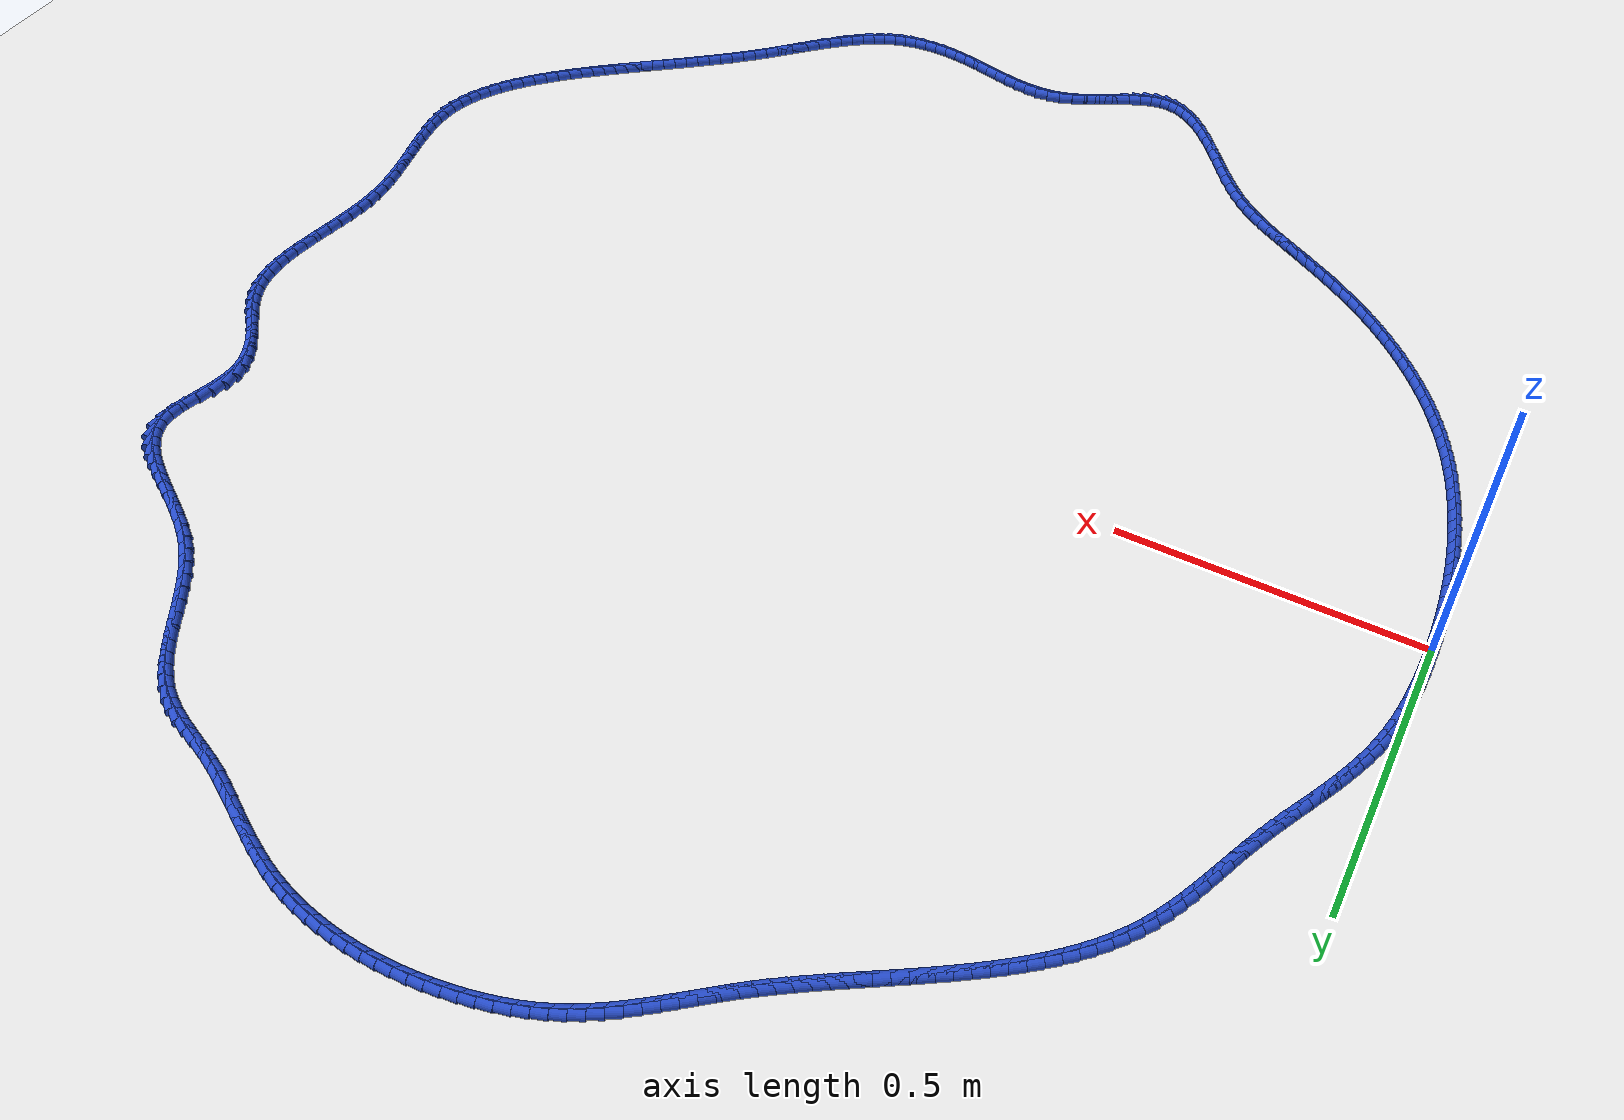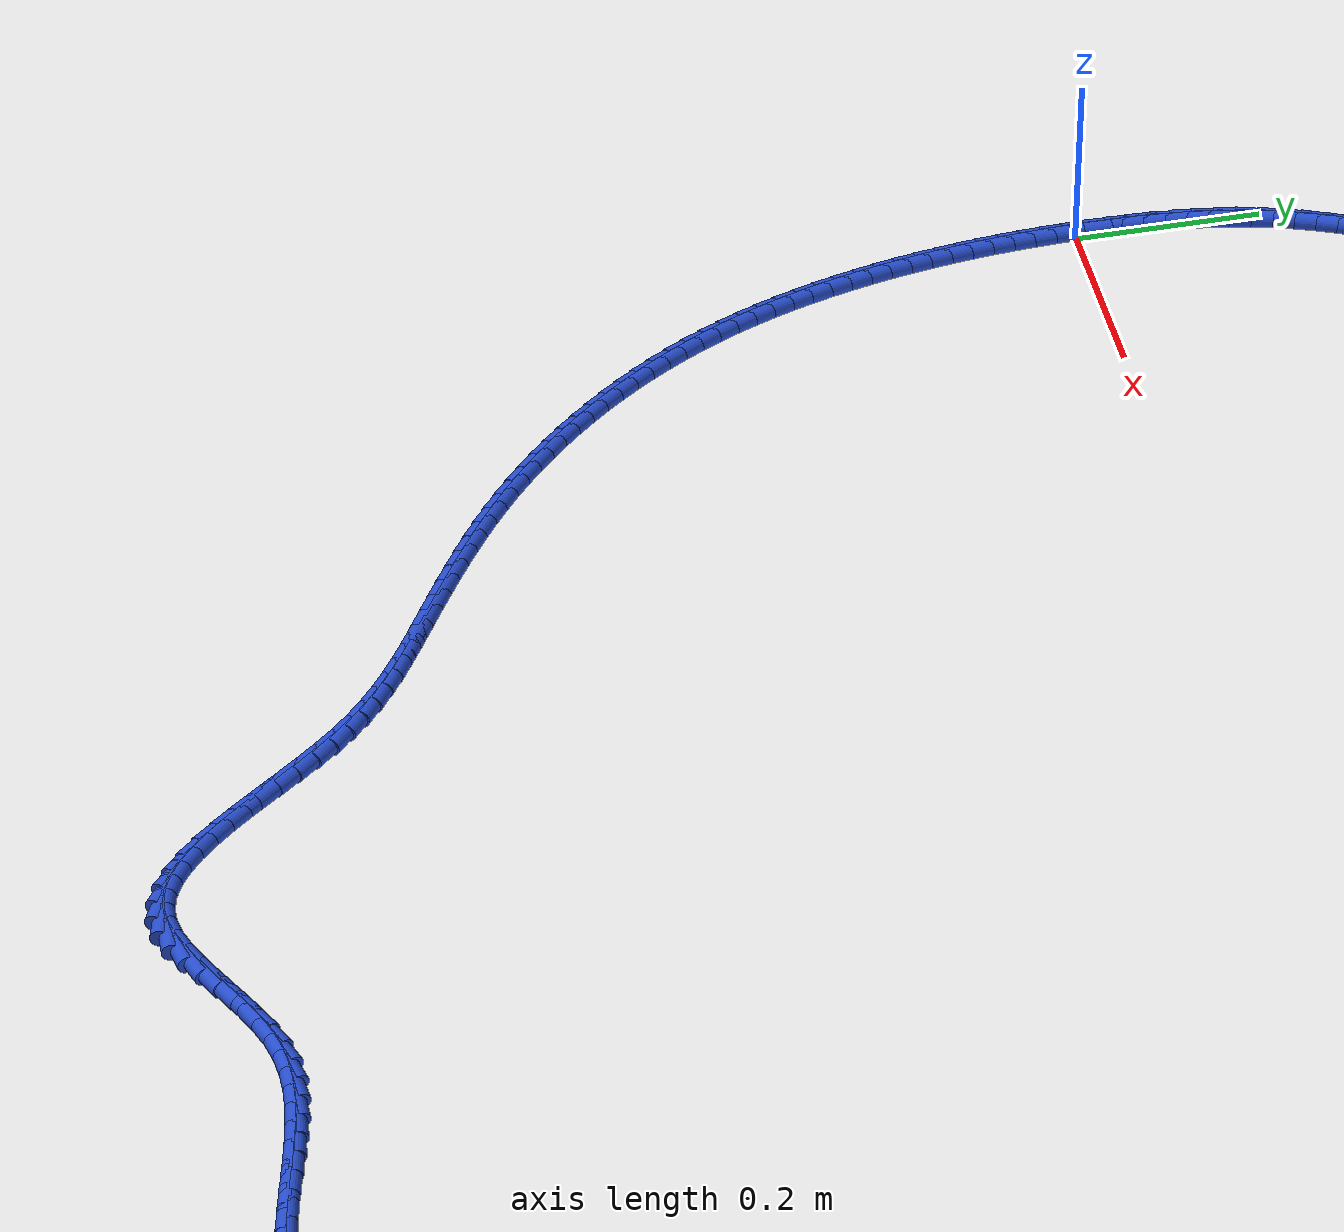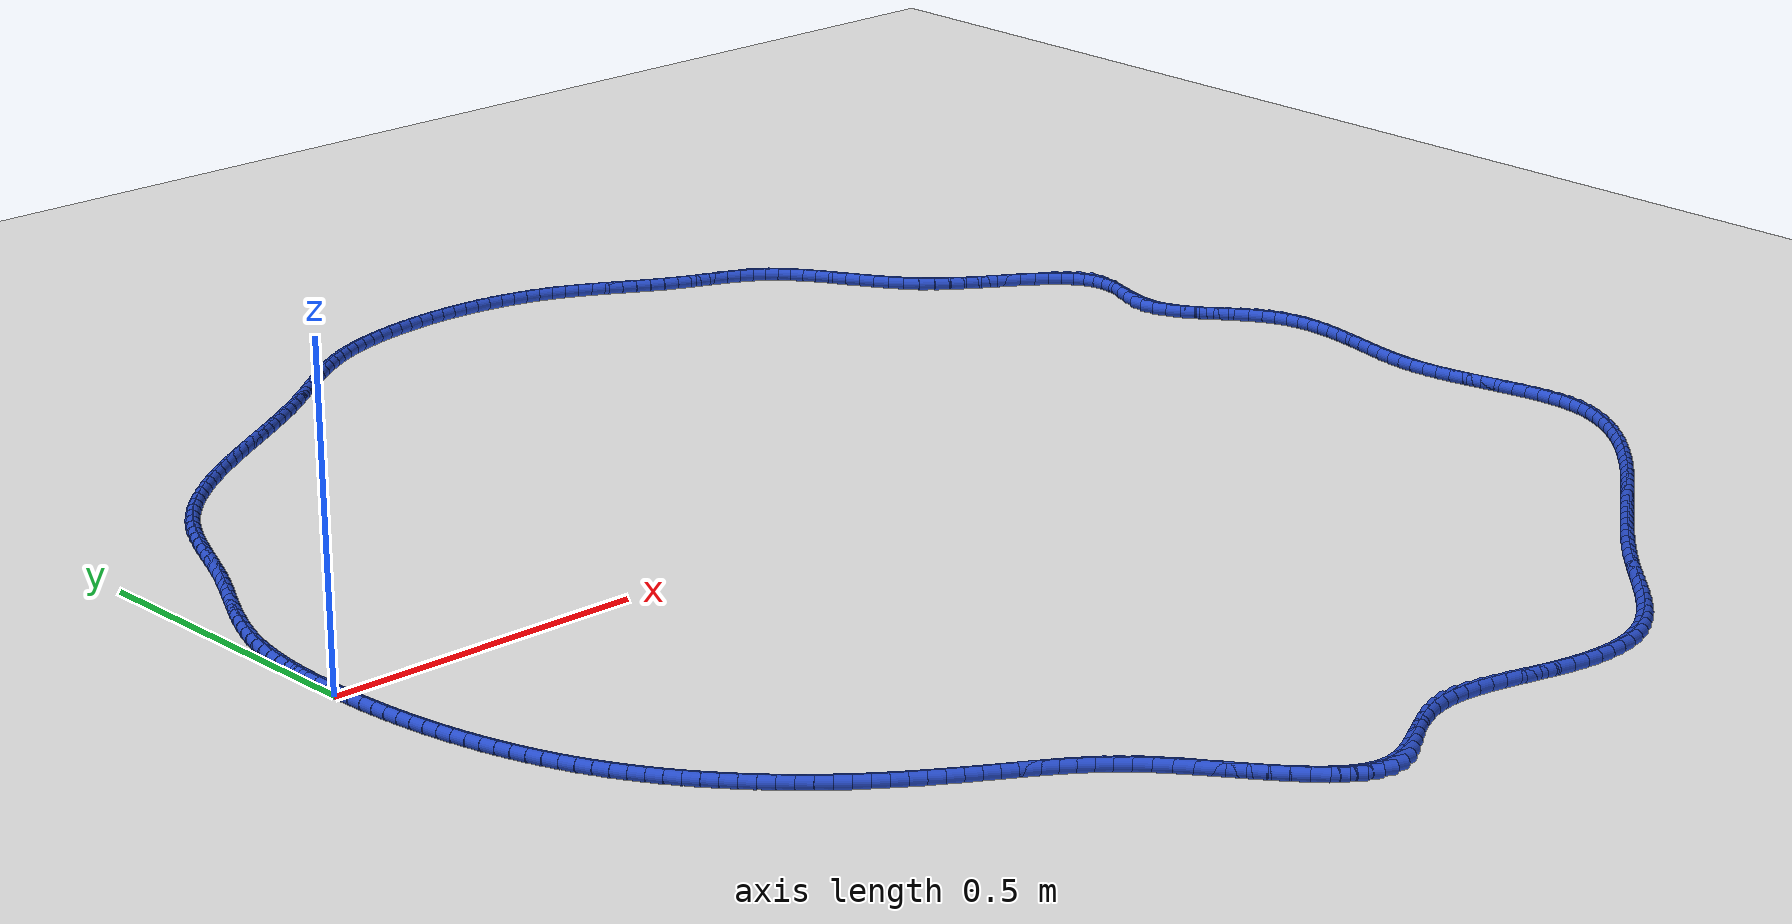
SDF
<sdf version="1.6">
 <world name="default">
  <light name="sun" type="directional">
   <pose>0 0 10 0 -0 0</pose>
   <diffuse>0.8 0.8 0.8 1</diffuse>
   <specular>0.2 0.2 0.2 1</specular>
   <attenuation>
    <range>1000</range>
    <constant>0.9</constant>
    <linear>0.01</linear>
    <quadratic>0.001</quadratic>
   </attenuation>
   <direction>-0.5 0.1 -0.9</direction>
  </light>
  <model name="ground_plane">
   <static>1</static>
   <link name="link">
    <collision name="collision">
     <geometry><plane><normal>0 0 1</normal><size>100 100</size></plane></geometry>
     <surface><friction><ode><mu>100</mu><mu2>50</mu2></ode></friction></surface>
    </collision>
    <visual name="visual">
     <cast_shadows>0</cast_shadows>
     <geometry><plane><normal>0 0 1</normal><size>100 100</size></plane></geometry>
     <material>
      <script><uri>file://media/materials/scripts/gazebo.material</uri><name>Gazebo/WhiteGlow</name></script>
     </material>
    </visual>
   </link>
  </model>
  <gravity>0 0 -9.8</gravity>
  <magnetic_field>6e-06 2.3e-05 -4.2e-05</magnetic_field>
  <atmosphere type="adiabatic"/>
  <physics name="default_physics" default="0" type="ode">
   <max_step_size>0.001</max_step_size>
   <real_time_factor>1</real_time_factor>
   <real_time_update_rate>1000</real_time_update_rate>
  </physics>
  <scene><ambient>0.4 0.4 0.4 1</ambient><background>0.7 0.7 0.7 1</background><shadows>1</shadows></scene>
  <spherical_coordinates>
   <surface_model>EARTH_WGS84</surface_model>
   <latitude_deg>0</latitude_deg>
   <longitude_deg>0</longitude_deg>
   <elevation>0</elevation>
   <heading_deg>0</heading_deg>
  </spherical_coordinates>
  <model name="line">
   <link name="link_0">
    <pose>6.5052130349130266e-18 4.163336342344337e-17 0.01 0 1.57 -1.5608195058965737</pose>
    <collision name="collision">
     <geometry><cylinder><radius>0.01</radius><length>0.08</length></cylinder></geometry>
    </collision>
    <visual name="visual">
     <material>
      <script><name>Gazebo/Blue</name><uri>file://media/materials/scripts/gazebo.material</uri></script>
     </material>
     <geometry><cylinder><radius>0.01</radius><length>0.08</length></cylinder></geometry>
    </visual>
   </link>
   <link name="link_1">
    <pose>-0.00023507645814420218 0.02356147924171589 0.01 0 1.57 1.5601489729837574</pose>
    <collision name="collision">
     <geometry><cylinder><radius>0.01</radius><length>0.08</length></cylinder></geometry>
    </collision>
    <visual name="visual">
     <material>
      <script><name>Gazebo/Blue</name><uri>file://media/materials/scripts/gazebo.material</uri></script>
     </material>
     <geometry><cylinder><radius>0.01</radius><length>0.08</length></cylinder></geometry>
    </visual>
   </link>
   <link name="link_2">
    <pose>1.6090893743628086e-05 0.04715023800560799 0.01 0 1.57 1.5363617328912627</pose>
    <collision name="collision">
     <geometry><cylinder><radius>0.01</radius><length>0.08</length></cylinder></geometry>
    </collision>
    <visual name="visual">
     <material>
      <script><name>Gazebo/Blue</name><uri>file://media/materials/scripts/gazebo.material</uri></script>
     </material>
     <geometry><cylinder><radius>0.01</radius><length>0.08</length></cylinder></geometry>
    </visual>
   </link>
   <link name="link_3">
    <pose>0.0008279500997930612 0.07071776715860631 0.01 0 1.57 1.509293770038079</pose>
    <collision name="collision">
     <geometry><cylinder><radius>0.01</radius><length>0.08</length></cylinder></geometry>
    </collision>
    <visual name="visual">
     <material>
      <script><name>Gazebo/Blue</name><uri>file://media/materials/scripts/gazebo.material</uri></script>
     </material>
     <geometry><cylinder><radius>0.01</radius><length>0.08</length></cylinder></geometry>
    </visual>
   </link>
   <link name="link_4">
    <pose>0.0022749492041336623 0.09421555756764083 0.01 0 1.57 1.4788141370203385</pose>
    <collision name="collision">
     <geometry><cylinder><radius>0.01</radius><length>0.08</length></cylinder></geometry>
    </collision>
    <visual name="visual">
     <material>
      <script><name>Gazebo/Blue</name><uri>file://media/materials/scripts/gazebo.material</uri></script>
     </material>
     <geometry><cylinder><radius>0.01</radius><length>0.08</length></cylinder></geometry>
    </visual>
   </link>
   <link name="link_5">
    <pose>0.0044315362508949956 0.11759510009964141 0.01 0 1.57 1.4447863616786807</pose>
    <collision name="collision">
     <geometry><cylinder><radius>0.01</radius><length>0.08</length></cylinder></geometry>
    </collision>
    <visual name="visual">
     <material>
      <script><name>Gazebo/Blue</name><uri>file://media/materials/scripts/gazebo.material</uri></script>
     </material>
     <geometry><cylinder><radius>0.01</radius><length>0.08</length></cylinder></geometry>
    </visual>
   </link>
   <link name="link_6">
    <pose>0.0073721592842066275 0.14080788562153812 0.01 0 1.57 1.4070785339423248</pose>
    <collision name="collision">
     <geometry><cylinder><radius>0.01</radius><length>0.08</length></cylinder></geometry>
    </collision>
    <visual name="visual">
     <material>
      <script><name>Gazebo/Blue</name><uri>file://media/materials/scripts/gazebo.material</uri></script>
     </material>
     <geometry><cylinder><radius>0.01</radius><length>0.08</length></cylinder></geometry>
    </visual>
   </link>
   <link name="link_7">
    <pose>0.011171266348198119 0.16380540500026086 0.01 0 1.57 1.3655762167708285</pose>
    <collision name="collision">
     <geometry><cylinder><radius>0.01</radius><length>0.08</length></cylinder></geometry>
    </collision>
    <visual name="visual">
     <material>
      <script><name>Gazebo/Blue</name><uri>file://media/materials/scripts/gazebo.material</uri></script>
     </material>
     <geometry><cylinder><radius>0.01</radius><length>0.08</length></cylinder></geometry>
    </visual>
   </link>
   <link name="link_8">
    <pose>0.015903305486999045 0.1865391491027396 0.01 0 1.57 1.320198483745123</pose>
    <collision name="collision">
     <geometry><cylinder><radius>0.01</radius><length>0.08</length></cylinder></geometry>
    </collision>
    <visual name="visual">
     <material>
      <script><name>Gazebo/Blue</name><uri>file://media/materials/scripts/gazebo.material</uri></script>
     </material>
     <geometry><cylinder><radius>0.01</radius><length>0.08</length></cylinder></geometry>
    </visual>
   </link>
   <link name="link_9">
    <pose>0.02164272474473896 0.20896060879590433 0.01 0 1.57 1.2716168211967784</pose>
    <collision name="collision">
     <geometry><cylinder><radius>0.01</radius><length>0.08</length></cylinder></geometry>
    </collision>
    <visual name="visual">
     <material>
      <script><name>Gazebo/Blue</name><uri>file://media/materials/scripts/gazebo.material</uri></script>
     </material>
     <geometry><cylinder><radius>0.01</radius><length>0.08</length></cylinder></geometry>
    </visual>
   </link>
   <link name="link_10">
    <pose>0.02844922572811799 0.23102829390374224 0.01 0 1.57 1.2264625580924882</pose>
    <collision name="collision">
     <geometry><cylinder><radius>0.01</radius><length>0.08</length></cylinder></geometry>
    </collision>
    <visual name="visual">
     <material>
      <script><name>Gazebo/Blue</name><uri>file://media/materials/scripts/gazebo.material</uri></script>
     </material>
     <geometry><cylinder><radius>0.01</radius><length>0.08</length></cylinder></geometry>
    </visual>
   </link>
   <link name="link_11">
    <pose>0.03624488986983642 0.2527662182132247 0.01 0 1.57 1.1884935130552572</pose>
    <collision name="collision">
     <geometry><cylinder><radius>0.01</radius><length>0.08</length></cylinder></geometry>
    </collision>
    <visual name="visual">
     <material>
      <script><name>Gazebo/Blue</name><uri>file://media/materials/scripts/gazebo.material</uri></script>
     </material>
     <geometry><cylinder><radius>0.01</radius><length>0.08</length></cylinder></geometry>
    </visual>
   </link>
   <link name="link_12">
    <pose>0.04487680689900698 0.2742340897967839 0.01 0 1.57 1.1578261310987938</pose>
    <collision name="collision">
     <geometry><cylinder><radius>0.01</radius><length>0.08</length></cylinder></geometry>
    </collision>
    <visual name="visual">
     <material>
      <script><name>Gazebo/Blue</name><uri>file://media/materials/scripts/gazebo.material</uri></script>
     </material>
     <geometry><cylinder><radius>0.01</radius><length>0.08</length></cylinder></geometry>
    </visual>
   </link>
   <link name="link_13">
    <pose>0.05419131224754835 0.2954919757545586 0.01 0 1.57 1.1344398003429639</pose>
    <collision name="collision">
     <geometry><cylinder><radius>0.01</radius><length>0.08</length></cylinder></geometry>
    </collision>
    <visual name="visual">
     <material>
      <script><name>Gazebo/Blue</name><uri>file://media/materials/scripts/gazebo.material</uri></script>
     </material>
     <geometry><cylinder><radius>0.01</radius><length>0.08</length></cylinder></geometry>
    </visual>
   </link>
   <link name="link_14">
    <pose>0.06403474134737928 0.3165999431866877 0.01 0 1.57 1.1182618441684526</pose>
    <collision name="collision">
     <geometry><cylinder><radius>0.01</radius><length>0.08</length></cylinder></geometry>
    </collision>
    <visual name="visual">
     <material>
      <script><name>Gazebo/Blue</name><uri>file://media/materials/scripts/gazebo.material</uri></script>
     </material>
     <geometry><cylinder><radius>0.01</radius><length>0.08</length></cylinder></geometry>
    </visual>
   </link>
   <link name="link_15">
    <pose>0.07425342963041842 0.33761805919331006 0.01 0 1.57 1.1092046508610245</pose>
    <collision name="collision">
     <geometry><cylinder><radius>0.01</radius><length>0.08</length></cylinder></geometry>
    </collision>
    <visual name="visual">
     <material>
      <script><name>Gazebo/Blue</name><uri>file://media/materials/scripts/gazebo.material</uri></script>
     </material>
     <geometry><cylinder><radius>0.01</radius><length>0.08</length></cylinder></geometry>
    </visual>
   </link>
   <link name="link_16">
    <pose>0.08469371252858456 0.35860639087456453 0.01 0 1.57 1.1071903687065814</pose>
    <collision name="collision">
     <geometry><cylinder><radius>0.01</radius><length>0.08</length></cylinder></geometry>
    </collision>
    <visual name="visual">
     <material>
      <script><name>Gazebo/Blue</name><uri>file://media/materials/scripts/gazebo.material</uri></script>
     </material>
     <geometry><cylinder><radius>0.01</radius><length>0.08</length></cylinder></geometry>
    </visual>
   </link>
   <link name="link_17">
    <pose>0.09520192547379637 0.37962500533059 0.01 0 1.57 1.1121639766737714</pose>
    <collision name="collision">
     <geometry><cylinder><radius>0.01</radius><length>0.08</length></cylinder></geometry>
    </collision>
    <visual name="visual">
     <material>
      <script><name>Gazebo/Blue</name><uri>file://media/materials/scripts/gazebo.material</uri></script>
     </material>
     <geometry><cylinder><radius>0.01</radius><length>0.08</length></cylinder></geometry>
    </visual>
   </link>
   <link name="link_18">
    <pose>0.10562440389797254 0.4007339696615254 0.01 0 1.57 1.1240956989621276</pose>
    <collision name="collision">
     <geometry><cylinder><radius>0.01</radius><length>0.08</length></cylinder></geometry>
    </collision>
    <visual name="visual">
     <material>
      <script><name>Gazebo/Blue</name><uri>file://media/materials/scripts/gazebo.material</uri></script>
     </material>
     <geometry><cylinder><radius>0.01</radius><length>0.08</length></cylinder></geometry>
    </visual>
   </link>
   <link name="link_19">
    <pose>0.11580748323303178 0.4219933509675095 0.01 0 1.57 1.1429529862613765</pose>
    <collision name="collision">
     <geometry><cylinder><radius>0.01</radius><length>0.08</length></cylinder></geometry>
    </collision>
    <visual name="visual">
     <material>
      <script><name>Gazebo/Blue</name><uri>file://media/materials/scripts/gazebo.material</uri></script>
     </material>
     <geometry><cylinder><radius>0.01</radius><length>0.08</length></cylinder></geometry>
    </visual>
   </link>
   <link name="link_20">
    <pose>0.12559792790075136 0.4434629971256428 0.01 0 1.57 1.1643094254880988</pose>
    <collision name="collision">
     <geometry><cylinder><radius>0.01</radius><length>0.08</length></cylinder></geometry>
    </collision>
    <visual name="visual">
     <material>
      <script><name>Gazebo/Blue</name><uri>file://media/materials/scripts/gazebo.material</uri></script>
     </material>
     <geometry><cylinder><radius>0.01</radius><length>0.08</length></cylinder></geometry>
    </visual>
   </link>
   <link name="link_21">
    <pose>0.13493556978566787 0.46515519653917853 0.01 0 1.57 1.1782902602926895</pose>
    <collision name="collision">
     <geometry><cylinder><radius>0.01</radius><length>0.08</length></cylinder></geometry>
    </collision>
    <visual name="visual">
     <material>
      <script><name>Gazebo/Blue</name><uri>file://media/materials/scripts/gazebo.material</uri></script>
     </material>
     <geometry><cylinder><radius>0.01</radius><length>0.08</length></cylinder></geometry>
    </visual>
   </link>
   <link name="link_22">
    <pose>0.14396893827497845 0.4869755887017988 0.01 0 1.57 1.1835920989453685</pose>
    <collision name="collision">
     <geometry><cylinder><radius>0.01</radius><length>0.08</length></cylinder></geometry>
    </collision>
    <visual name="visual">
     <material>
      <script><name>Gazebo/Blue</name><uri>file://media/materials/scripts/gazebo.material</uri></script>
     </material>
     <geometry><cylinder><radius>0.01</radius><length>0.08</length></cylinder></geometry>
    </visual>
   </link>
   <link name="link_23">
    <pose>0.15287496461246847 0.5088152991480044 0.01 0 1.57 1.1802022733946649</pose>
    <collision name="collision">
     <geometry><cylinder><radius>0.01</radius><length>0.08</length></cylinder></geometry>
    </collision>
    <visual name="visual">
     <material>
      <script><name>Gazebo/Blue</name><uri>file://media/materials/scripts/gazebo.material</uri></script>
     </material>
     <geometry><cylinder><radius>0.01</radius><length>0.08</length></cylinder></geometry>
    </visual>
   </link>
   <link name="link_24">
    <pose>0.1618305800419234 0.5305654534122963 0.01 0 1.57 1.1680357168658686</pose>
    <collision name="collision">
     <geometry><cylinder><radius>0.01</radius><length>0.08</length></cylinder></geometry>
    </collision>
    <visual name="visual">
     <material>
      <script><name>Gazebo/Blue</name><uri>file://media/materials/scripts/gazebo.material</uri></script>
     </material>
     <geometry><cylinder><radius>0.01</radius><length>0.08</length></cylinder></geometry>
    </visual>
   </link>
   <link name="link_25">
    <pose>0.17101271580712882 0.5521171770291747 0.01 0 1.57 1.1469407934667508</pose>
    <collision name="collision">
     <geometry><cylinder><radius>0.01</radius><length>0.08</length></cylinder></geometry>
    </collision>
    <visual name="visual">
     <material>
      <script><name>Gazebo/Blue</name><uri>file://media/materials/scripts/gazebo.material</uri></script>
     </material>
     <geometry><cylinder><radius>0.01</radius><length>0.08</length></cylinder></geometry>
    </visual>
   </link>
   <link name="link_26">
    <pose>0.18059830315186992 0.5733615955331403 0.01 0 1.57 1.1167253286300085</pose>
    <collision name="collision">
     <geometry><cylinder><radius>0.01</radius><length>0.08</length></cylinder></geometry>
    </collision>
    <visual name="visual">
     <material>
      <script><name>Gazebo/Blue</name><uri>file://media/materials/scripts/gazebo.material</uri></script>
     </material>
     <geometry><cylinder><radius>0.01</radius><length>0.08</length></cylinder></geometry>
    </visual>
   </link>
   <link name="link_27">
    <pose>0.19076427331993226 0.5941898344586938 0.01 0 1.57 1.0772063020759166</pose>
    <collision name="collision">
     <geometry><cylinder><radius>0.01</radius><length>0.08</length></cylinder></geometry>
    </collision>
    <visual name="visual">
     <material>
      <script><name>Gazebo/Blue</name><uri>file://media/materials/scripts/gazebo.material</uri></script>
     </material>
     <geometry><cylinder><radius>0.01</radius><length>0.08</length></cylinder></geometry>
    </visual>
   </link>
   <link name="link_28">
    <pose>0.2016875575551014 0.6144930193403363 0.01 0 1.57 1.0282869178722294</pose>
    <collision name="collision">
     <geometry><cylinder><radius>0.01</radius><length>0.08</length></cylinder></geometry>
    </collision>
    <visual name="visual">
     <material>
      <script><name>Gazebo/Blue</name><uri>file://media/materials/scripts/gazebo.material</uri></script>
     </material>
     <geometry><cylinder><radius>0.01</radius><length>0.08</length></cylinder></geometry>
    </visual>
   </link>
   <link name="link_29">
    <pose>0.2135450871011626 0.634162275712568 0.01 0 1.57 0.9711285834671429</pose>
    <collision name="collision">
     <geometry><cylinder><radius>0.01</radius><length>0.08</length></cylinder></geometry>
    </collision>
    <visual name="visual">
     <material>
      <script><name>Gazebo/Blue</name><uri>file://media/materials/scripts/gazebo.material</uri></script>
     </material>
     <geometry><cylinder><radius>0.01</radius><length>0.08</length></cylinder></geometry>
    </visual>
   </link>
   <link name="link_30">
    <pose>0.2264924099962033 0.6531008246108365 0.01 0 1.57 0.9143689457426699</pose>
    <collision name="collision">
     <geometry><cylinder><radius>0.01</radius><length>0.08</length></cylinder></geometry>
    </collision>
    <visual name="visual">
     <material>
      <script><name>Gazebo/Blue</name><uri>file://media/materials/scripts/gazebo.material</uri></script>
     </material>
     <geometry><cylinder><radius>0.01</radius><length>0.08</length></cylinder></geometry>
    </visual>
   </link>
   <link name="link_31">
    <pose>0.2405179376254366 0.6713064286267854 0.01 0 1.57 0.8621454481881927</pose>
    <collision name="collision">
     <geometry><cylinder><radius>0.01</radius><length>0.08</length></cylinder></geometry>
    </collision>
    <visual name="visual">
     <material>
      <script><name>Gazebo/Blue</name><uri>file://media/materials/scripts/gazebo.material</uri></script>
     </material>
     <geometry><cylinder><radius>0.01</radius><length>0.08</length></cylinder></geometry>
    </visual>
   </link>
   <link name="link_32">
    <pose>0.2555314544437972 0.6888213260084713 0.01 0 1.57 0.814551818937603</pose>
    <collision name="collision">
     <geometry><cylinder><radius>0.01</radius><length>0.08</length></cylinder></geometry>
    </collision>
    <visual name="visual">
     <material>
      <script><name>Gazebo/Blue</name><uri>file://media/materials/scripts/gazebo.material</uri></script>
     </material>
     <geometry><cylinder><radius>0.01</radius><length>0.08</length></cylinder></geometry>
    </visual>
   </link>
   <link name="link_33">
    <pose>0.2714422870578083 0.7056880139878459 0.01 0 1.57 0.7715566989743862</pose>
    <collision name="collision">
     <geometry><cylinder><radius>0.01</radius><length>0.08</length></cylinder></geometry>
    </collision>
    <visual name="visual">
     <material>
      <script><name>Gazebo/Blue</name><uri>file://media/materials/scripts/gazebo.material</uri></script>
     </material>
     <geometry><cylinder><radius>0.01</radius><length>0.08</length></cylinder></geometry>
    </visual>
   </link>
   <link name="link_34">
    <pose>0.2881597620739932 0.7219489897968604 0.01 0 1.57 0.7330578426366996</pose>
    <collision name="collision">
     <geometry><cylinder><radius>0.01</radius><length>0.08</length></cylinder></geometry>
    </collision>
    <visual name="visual">
     <material>
      <script><name>Gazebo/Blue</name><uri>file://media/materials/scripts/gazebo.material</uri></script>
     </material>
     <geometry><cylinder><radius>0.01</radius><length>0.08</length></cylinder></geometry>
    </visual>
   </link>
   <link name="link_35">
    <pose>0.30559320609887525 0.737646750667467 0.01 0 1.57 0.6989098247970498</pose>
    <collision name="collision">
     <geometry><cylinder><radius>0.01</radius><length>0.08</length></cylinder></geometry>
    </collision>
    <visual name="visual">
     <material>
      <script><name>Gazebo/Blue</name><uri>file://media/materials/scripts/gazebo.material</uri></script>
     </material>
     <geometry><cylinder><radius>0.01</radius><length>0.08</length></cylinder></geometry>
    </visual>
   </link>
   <link name="link_36">
    <pose>0.32365194573897776 0.7528237938316167 0.01 0 1.57 0.668946846342265</pose>
    <collision name="collision">
     <geometry><cylinder><radius>0.01</radius><length>0.08</length></cylinder></geometry>
    </collision>
    <visual name="visual">
     <material>
      <script><name>Gazebo/Blue</name><uri>file://media/materials/scripts/gazebo.material</uri></script>
     </material>
     <geometry><cylinder><radius>0.01</radius><length>0.08</length></cylinder></geometry>
    </visual>
   </link>
   <link name="link_37">
    <pose>0.3422453076008239 0.7675226165212613 0.01 0 1.57 0.6430005622383067</pose>
    <collision name="collision">
     <geometry><cylinder><radius>0.01</radius><length>0.08</length></cylinder></geometry>
    </collision>
    <visual name="visual">
     <material>
      <script><name>Gazebo/Blue</name><uri>file://media/materials/scripts/gazebo.material</uri></script>
     </material>
     <geometry><cylinder><radius>0.01</radius><length>0.08</length></cylinder></geometry>
    </visual>
   </link>
   <link name="link_38">
    <pose>0.36128261829093694 0.7817857159683524 0.01 0 1.57 0.6209135249268366</pose>
    <collision name="collision">
     <geometry><cylinder><radius>0.01</radius><length>0.08</length></cylinder></geometry>
    </collision>
    <visual name="visual">
     <material>
      <script><name>Gazebo/Blue</name><uri>file://media/materials/scripts/gazebo.material</uri></script>
     </material>
     <geometry><cylinder><radius>0.01</radius><length>0.08</length></cylinder></geometry>
    </visual>
   </link>
   <link name="link_39">
    <pose>0.38067320441584046 0.7956555894048418 0.01 0 1.57 0.6025491223568439</pose>
    <collision name="collision">
     <geometry><cylinder><radius>0.01</radius><length>0.08</length></cylinder></geometry>
    </collision>
    <visual name="visual">
     <material>
      <script><name>Gazebo/Blue</name><uri>file://media/materials/scripts/gazebo.material</uri></script>
     </material>
     <geometry><cylinder><radius>0.01</radius><length>0.08</length></cylinder></geometry>
    </visual>
   </link>
   <link name="link_40">
    <pose>0.4003263925820576 0.8091747340626807 0.01 0 1.57 0.587798938012503</pose>
    <collision name="collision">
     <geometry><cylinder><radius>0.01</radius><length>0.08</length></cylinder></geometry>
    </collision>
    <visual name="visual">
     <material>
      <script><name>Gazebo/Blue</name><uri>file://media/materials/scripts/gazebo.material</uri></script>
     </material>
     <geometry><cylinder><radius>0.01</radius><length>0.08</length></cylinder></geometry>
    </visual>
   </link>
   <link name="link_41">
    <pose>0.42015150939611146 0.8223856471738207 0.01 0 1.57 0.5765883842372478</pose>
    <collision name="collision">
     <geometry><cylinder><radius>0.01</radius><length>0.08</length></cylinder></geometry>
    </collision>
    <visual name="visual">
     <material>
      <script><name>Gazebo/Blue</name><uri>file://media/materials/scripts/gazebo.material</uri></script>
     </material>
     <geometry><cylinder><radius>0.01</radius><length>0.08</length></cylinder></geometry>
    </visual>
   </link>
   <link name="link_42">
    <pose>0.44005788146452557 0.8353308259702136 0.01 0 1.57 0.5688060805404918</pose>
    <collision name="collision">
     <geometry><cylinder><radius>0.01</radius><length>0.08</length></cylinder></geometry>
    </collision>
    <visual name="visual">
     <material>
      <script><name>Gazebo/Blue</name><uri>file://media/materials/scripts/gazebo.material</uri></script>
     </material>
     <geometry><cylinder><radius>0.01</radius><length>0.08</length></cylinder></geometry>
    </visual>
   </link>
   <link name="link_43">
    <pose>0.45996256871853025 0.8480556020987096 0.01 0 1.57 0.5640231631581542</pose>
    <collision name="collision">
     <geometry><cylinder><radius>0.01</radius><length>0.08</length></cylinder></geometry>
    </collision>
    <visual name="visual">
     <material>
      <script><name>Gazebo/Blue</name><uri>file://media/materials/scripts/gazebo.material</uri></script>
     </material>
     <geometry><cylinder><radius>0.01</radius><length>0.08</length></cylinder></geometry>
    </visual>
   </link>
   <link name="link_44">
    <pose>0.4798283466913867 0.860622062869267 0.01 0 1.57 0.5621269856889552</pose>
    <collision name="collision">
     <geometry><cylinder><radius>0.01</radius><length>0.08</length></cylinder></geometry>
    </collision>
    <visual name="visual">
     <material>
      <script><name>Gazebo/Blue</name><uri>file://media/materials/scripts/gazebo.material</uri></script>
     </material>
     <geometry><cylinder><radius>0.01</radius><length>0.08</length></cylinder></geometry>
    </visual>
   </link>
   <link name="link_45">
    <pose>0.49963472901391875 0.8730984304322789 0.01 0 1.57 0.5631585215495446</pose>
    <collision name="collision">
     <geometry><cylinder><radius>0.01</radius><length>0.08</length></cylinder></geometry>
    </collision>
    <visual name="visual">
     <material>
      <script><name>Gazebo/Blue</name><uri>file://media/materials/scripts/gazebo.material</uri></script>
     </material>
     <geometry><cylinder><radius>0.01</radius><length>0.08</length></cylinder></geometry>
    </visual>
   </link>
   <link name="link_46">
    <pose>0.5193612544176707 0.8855529361380439 0.01 0 1.57 0.5671451008149884</pose>
    <collision name="collision">
     <geometry><cylinder><radius>0.01</radius><length>0.08</length></cylinder></geometry>
    </collision>
    <visual name="visual">
     <material>
      <script><name>Gazebo/Blue</name><uri>file://media/materials/scripts/gazebo.material</uri></script>
     </material>
     <geometry><cylinder><radius>0.01</radius><length>0.08</length></cylinder></geometry>
    </visual>
   </link>
   <link name="link_47">
    <pose>0.538987461634187 0.8980538113368601 0.01 0 1.57 0.5740994297672182</pose>
    <collision name="collision">
     <geometry><cylinder><radius>0.01</radius><length>0.08</length></cylinder></geometry>
    </collision>
    <visual name="visual">
     <material>
      <script><name>Gazebo/Blue</name><uri>file://media/materials/scripts/gazebo.material</uri></script>
     </material>
     <geometry><cylinder><radius>0.01</radius><length>0.08</length></cylinder></geometry>
    </visual>
   </link>
   <link name="link_48">
    <pose>0.5584928893950118 0.9106692873790263 0.01 0 1.57 0.5840182460591699</pose>
    <collision name="collision">
     <geometry><cylinder><radius>0.01</radius><length>0.08</length></cylinder></geometry>
    </collision>
    <visual name="visual">
     <material>
      <script><name>Gazebo/Blue</name><uri>file://media/materials/scripts/gazebo.material</uri></script>
     </material>
     <geometry><cylinder><radius>0.01</radius><length>0.08</length></cylinder></geometry>
    </visual>
   </link>
   <link name="link_49">
    <pose>0.5778570764316895 0.9234675956148408 0.01 0 1.57 0.5968803896489623</pose>
    <collision name="collision">
     <geometry><cylinder><radius>0.01</radius><length>0.08</length></cylinder></geometry>
    </collision>
    <visual name="visual">
     <material>
      <script><name>Gazebo/Blue</name><uri>file://media/materials/scripts/gazebo.material</uri></script>
     </material>
     <geometry><cylinder><radius>0.01</radius><length>0.08</length></cylinder></geometry>
    </visual>
   </link>
   <link name="link_50">
    <pose>0.5970595614757639 0.9365169673946019 0.01 0 1.57 0.6126443735051876</pose>
    <collision name="collision">
     <geometry><cylinder><radius>0.01</radius><length>0.08</length></cylinder></geometry>
    </collision>
    <visual name="visual">
     <material>
      <script><name>Gazebo/Blue</name><uri>file://media/materials/scripts/gazebo.material</uri></script>
     </material>
     <geometry><cylinder><radius>0.01</radius><length>0.08</length></cylinder></geometry>
    </visual>
   </link>
   <link name="link_51">
    <pose>0.6160798832587795 0.9498856340686082 0.01 0 1.57 0.63124560575637</pose>
    <collision name="collision">
     <geometry><cylinder><radius>0.01</radius><length>0.08</length></cylinder></geometry>
    </collision>
    <visual name="visual">
     <material>
      <script><name>Gazebo/Blue</name><uri>file://media/materials/scripts/gazebo.material</uri></script>
     </material>
     <geometry><cylinder><radius>0.01</radius><length>0.08</length></cylinder></geometry>
    </visual>
   </link>
   <link name="link_52">
    <pose>0.6348975805122806 0.9636418269871582 0.01 0 1.57 0.6507751650396512</pose>
    <collision name="collision">
     <geometry><cylinder><radius>0.01</radius><length>0.08</length></cylinder></geometry>
    </collision>
    <visual name="visual">
     <material>
      <script><name>Gazebo/Blue</name><uri>file://media/materials/scripts/gazebo.material</uri></script>
     </material>
     <geometry><cylinder><radius>0.01</radius><length>0.08</length></cylinder></geometry>
    </visual>
   </link>
   <link name="link_53">
    <pose>0.6535102891567073 0.9778140693779296 0.01 0 1.57 0.6638762733937609</pose>
    <collision name="collision">
     <geometry><cylinder><radius>0.01</radius><length>0.08</length></cylinder></geometry>
    </collision>
    <visual name="visual">
     <material>
      <script><name>Gazebo/Blue</name><uri>file://media/materials/scripts/gazebo.material</uri></script>
     </material>
     <geometry><cylinder><radius>0.01</radius><length>0.08</length></cylinder></geometry>
    </visual>
   </link>
   <link name="link_54">
    <pose>0.6719887730205872 0.9922704301594752 0.01 0 1.57 0.6687994790913384</pose>
    <collision name="collision">
     <geometry><cylinder><radius>0.01</radius><length>0.08</length></cylinder></geometry>
    </collision>
    <visual name="visual">
     <material>
      <script><name>Gazebo/Blue</name><uri>file://media/materials/scripts/gazebo.material</uri></script>
     </material>
     <geometry><cylinder><radius>0.01</radius><length>0.08</length></cylinder></geometry>
    </visual>
   </link>
   <link name="link_55">
    <pose>0.690422264580532 1.0068384550869462 0.01 0 1.57 0.6656016224878809</pose>
    <collision name="collision">
     <geometry><cylinder><radius>0.01</radius><length>0.08</length></cylinder></geometry>
    </collision>
    <visual name="visual">
     <material>
      <script><name>Gazebo/Blue</name><uri>file://media/materials/scripts/gazebo.material</uri></script>
     </material>
     <geometry><cylinder><radius>0.01</radius><length>0.08</length></cylinder></geometry>
    </visual>
   </link>
   <link name="link_56">
    <pose>0.7088999963138635 1.0213456899139362 0.01 0 1.57 0.6542654524097217</pose>
    <collision name="collision">
     <geometry><cylinder><radius>0.01</radius><length>0.08</length></cylinder></geometry>
    </collision>
    <visual name="visual">
     <material>
      <script><name>Gazebo/Blue</name><uri>file://media/materials/scripts/gazebo.material</uri></script>
     </material>
     <geometry><cylinder><radius>0.01</radius><length>0.08</length></cylinder></geometry>
    </visual>
   </link>
   <link name="link_57">
    <pose>0.7275112006979023 1.0356196803940385 0.01 0 1.57 0.634705744093836</pose>
    <collision name="collision">
     <geometry><cylinder><radius>0.01</radius><length>0.08</length></cylinder></geometry>
    </collision>
    <visual name="visual">
     <material>
      <script><name>Gazebo/Blue</name><uri>file://media/materials/scripts/gazebo.material</uri></script>
     </material>
     <geometry><cylinder><radius>0.01</radius><length>0.08</length></cylinder></geometry>
    </visual>
   </link>
   <link name="link_58">
    <pose>0.7463451102099701 1.0494879722808468 0.01 0 1.57 0.6067907267437276</pose>
    <collision name="collision">
     <geometry><cylinder><radius>0.01</radius><length>0.08</length></cylinder></geometry>
    </collision>
    <visual name="visual">
     <material>
      <script><name>Gazebo/Blue</name><uri>file://media/materials/scripts/gazebo.material</uri></script>
     </material>
     <geometry><cylinder><radius>0.01</radius><length>0.08</length></cylinder></geometry>
    </visual>
   </link>
   <link name="link_59">
    <pose>0.7654909573273879 1.0627781113279535 0.01 0 1.57 0.5703809628463034</pose>
    <collision name="collision">
     <geometry><cylinder><radius>0.01</radius><length>0.08</length></cylinder></geometry>
    </collision>
    <visual name="visual">
     <material>
      <script><name>Gazebo/Blue</name><uri>file://media/materials/scripts/gazebo.material</uri></script>
     </material>
     <geometry><cylinder><radius>0.01</radius><length>0.08</length></cylinder></geometry>
    </visual>
   </link>
   <link name="link_60">
    <pose>0.7850379745274775 1.0753176432889537 0.01 0 1.57 0.5253883561052721</pose>
    <collision name="collision">
     <geometry><cylinder><radius>0.01</radius><length>0.08</length></cylinder></geometry>
    </collision>
    <visual name="visual">
     <material>
      <script><name>Gazebo/Blue</name><uri>file://media/materials/scripts/gazebo.material</uri></script>
     </material>
     <geometry><cylinder><radius>0.01</radius><length>0.08</length></cylinder></geometry>
    </visual>
   </link>
   <link name="link_61">
    <pose>0.8050753942875601 1.08693411391744 0.01 0 1.57 0.47203093881704056</pose>
    <collision name="collision">
     <geometry><cylinder><radius>0.01</radius><length>0.08</length></cylinder></geometry>
    </collision>
    <visual name="visual">
     <material>
      <script><name>Gazebo/Blue</name><uri>file://media/materials/scripts/gazebo.material</uri></script>
     </material>
     <geometry><cylinder><radius>0.01</radius><length>0.08</length></cylinder></geometry>
    </visual>
   </link>
   <link name="link_62">
    <pose>0.8256902185933533 1.0974584665835798 0.01 0 1.57 0.4158006331303245</pose>
    <collision name="collision">
     <geometry><cylinder><radius>0.01</radius><length>0.08</length></cylinder></geometry>
    </collision>
    <visual name="visual">
     <material>
      <script><name>Gazebo/Blue</name><uri>file://media/materials/scripts/gazebo.material</uri></script>
     </material>
     <geometry><cylinder><radius>0.01</radius><length>0.08</length></cylinder></geometry>
    </visual>
   </link>
   <link name="link_63">
    <pose>0.8469019809973135 1.1068244165607253 0.01 0 1.57 0.3629378963648534</pose>
    <collision name="collision">
     <geometry><cylinder><radius>0.01</radius><length>0.08</length></cylinder></geometry>
    </collision>
    <visual name="visual">
     <material>
      <script><name>Gazebo/Blue</name><uri>file://media/materials/scripts/gazebo.material</uri></script>
     </material>
     <geometry><cylinder><radius>0.01</radius><length>0.08</length></cylinder></geometry>
    </visual>
   </link>
   <link name="link_64">
    <pose>0.8686523161829901 1.1150843392811527 0.01 0 1.57 0.3137983563629217</pose>
    <collision name="collision">
     <geometry><cylinder><radius>0.01</radius><length>0.08</length></cylinder></geometry>
    </collision>
    <visual name="visual">
     <material>
      <script><name>Gazebo/Blue</name><uri>file://media/materials/scripts/gazebo.material</uri></script>
     </material>
     <geometry><cylinder><radius>0.01</radius><length>0.08</length></cylinder></geometry>
    </visual>
   </link>
   <link name="link_65">
    <pose>0.8908785287324718 1.1222972060434786 0.01 0 1.57 0.26832303508822736</pose>
    <collision name="collision">
     <geometry><cylinder><radius>0.01</radius><length>0.08</length></cylinder></geometry>
    </collision>
    <visual name="visual">
     <material>
      <script><name>Gazebo/Blue</name><uri>file://media/materials/scripts/gazebo.material</uri></script>
     </material>
     <geometry><cylinder><radius>0.01</radius><length>0.08</length></cylinder></geometry>
    </visual>
   </link>
   <link name="link_66">
    <pose>0.9135179232278486 1.1285219881463218 0.01 0 1.57 0.22639869798866794</pose>
    <collision name="collision">
     <geometry><cylinder><radius>0.01</radius><length>0.08</length></cylinder></geometry>
    </collision>
    <visual name="visual">
     <material>
      <script><name>Gazebo/Blue</name><uri>file://media/materials/scripts/gazebo.material</uri></script>
     </material>
     <geometry><cylinder><radius>0.01</radius><length>0.08</length></cylinder></geometry>
    </visual>
   </link>
   <link name="link_67">
    <pose>0.936507804251209 1.1338176568882987 0.01 0 1.57 0.18787665477764348</pose>
    <collision name="collision">
     <geometry><cylinder><radius>0.01</radius><length>0.08</length></cylinder></geometry>
    </collision>
    <visual name="visual">
     <material>
      <script><name>Gazebo/Blue</name><uri>file://media/materials/scripts/gazebo.material</uri></script>
     </material>
     <geometry><cylinder><radius>0.01</radius><length>0.08</length></cylinder></geometry>
    </visual>
   </link>
   <link name="link_68">
    <pose>0.9597854765928584 1.1382431812270104 0.01 0 1.57 0.151939371677457</pose>
    <collision name="collision">
     <geometry><cylinder><radius>0.01</radius><length>0.08</length></cylinder></geometry>
    </collision>
    <visual name="visual">
     <material>
      <script><name>Gazebo/Blue</name><uri>file://media/materials/scripts/gazebo.material</uri></script>
     </material>
     <geometry><cylinder><radius>0.01</radius><length>0.08</length></cylinder></geometry>
    </visual>
   </link>
   <link name="link_69">
    <pose>0.983289615424861 1.1418421225704836 0.01 0 1.57 0.11622041618310598</pose>
    <collision name="collision">
     <geometry><cylinder><radius>0.01</radius><length>0.08</length></cylinder></geometry>
    </collision>
    <visual name="visual">
     <material>
      <script><name>Gazebo/Blue</name><uri>file://media/materials/scripts/gazebo.material</uri></script>
     </material>
     <geometry><cylinder><radius>0.01</radius><length>0.08</length></cylinder></geometry>
    </visual>
   </link>
   <link name="link_70">
    <pose>1.0069635273815714 1.1446059696219801 0.01 0 1.57 0.08008954982298973</pose>
    <collision name="collision">
     <geometry><cylinder><radius>0.01</radius><length>0.08</length></cylinder></geometry>
    </collision>
    <visual name="visual">
     <material>
      <script><name>Gazebo/Blue</name><uri>file://media/materials/scripts/gazebo.material</uri></script>
     </material>
     <geometry><cylinder><radius>0.01</radius><length>0.08</length></cylinder></geometry>
    </visual>
   </link>
   <link name="link_71">
    <pose>1.0307514965528453 1.1465152213047434 0.01 0 1.57 0.04338221477648475</pose>
    <collision name="collision">
     <geometry><cylinder><radius>0.01</radius><length>0.08</length></cylinder></geometry>
    </collision>
    <visual name="visual">
     <material>
      <script><name>Gazebo/Blue</name><uri>file://media/materials/scripts/gazebo.material</uri></script>
     </material>
     <geometry><cylinder><radius>0.01</radius><length>0.08</length></cylinder></geometry>
    </visual>
   </link>
   <link name="link_72">
    <pose>1.0545978070285376 1.1475503765420183 0.01 0 1.57 0.005935529090897447</pose>
    <collision name="collision">
     <geometry><cylinder><radius>0.01</radius><length>0.08</length></cylinder></geometry>
    </collision>
    <visual name="visual">
     <material>
      <script><name>Gazebo/Blue</name><uri>file://media/materials/scripts/gazebo.material</uri></script>
     </material>
     <geometry><cylinder><radius>0.01</radius><length>0.08</length></cylinder></geometry>
    </visual>
   </link>
   <link name="link_73">
    <pose>1.0784467428985038 1.1476919342570486 0.01 0 1.57 -0.032411989409883456</pose>
    <collision name="collision">
     <geometry><cylinder><radius>0.01</radius><length>0.08</length></cylinder></geometry>
    </collision>
    <visual name="visual">
     <material>
      <script><name>Gazebo/Blue</name><uri>file://media/materials/scripts/gazebo.material</uri></script>
     </material>
     <geometry><cylinder><radius>0.01</radius><length>0.08</length></cylinder></geometry>
    </visual>
   </link>
   <link name="link_74">
    <pose>1.1022425882525988 1.1469203933730785 0.01 0 1.57 -0.07182026784524694</pose>
    <collision name="collision">
     <geometry><cylinder><radius>0.01</radius><length>0.08</length></cylinder></geometry>
    </collision>
    <visual name="visual">
     <material>
      <script><name>Gazebo/Blue</name><uri>file://media/materials/scripts/gazebo.material</uri></script>
     </material>
     <geometry><cylinder><radius>0.01</radius><length>0.08</length></cylinder></geometry>
    </visual>
   </link>
   <link name="link_75">
    <pose>1.1259296271806787 1.1452162528133523 0.01 0 1.57 -0.11244699908991783</pose>
    <collision name="collision">
     <geometry><cylinder><radius>0.01</radius><length>0.08</length></cylinder></geometry>
    </collision>
    <visual name="visual">
     <material>
      <script><name>Gazebo/Blue</name><uri>file://media/materials/scripts/gazebo.material</uri></script>
     </material>
     <geometry><cylinder><radius>0.01</radius><length>0.08</length></cylinder></geometry>
    </visual>
   </link>
   <link name="link_76">
    <pose>1.1494521437725977 1.142560011501114 0.01 0 1.57 -0.1544463301866992</pose>
    <collision name="collision">
     <geometry><cylinder><radius>0.01</radius><length>0.08</length></cylinder></geometry>
    </collision>
    <visual name="visual">
     <material>
      <script><name>Gazebo/Blue</name><uri>file://media/materials/scripts/gazebo.material</uri></script>
     </material>
     <geometry><cylinder><radius>0.01</radius><length>0.08</length></cylinder></geometry>
    </visual>
   </link>
   <link name="link_77">
    <pose>1.1727544221182122 1.1389321683596079 0.01 0 1.57 -0.1979667975714191</pose>
    <collision name="collision">
     <geometry><cylinder><radius>0.01</radius><length>0.08</length></cylinder></geometry>
    </collision>
    <visual name="visual">
     <material>
      <script><name>Gazebo/Blue</name><uri>file://media/materials/scripts/gazebo.material</uri></script>
     </material>
     <geometry><cylinder><radius>0.01</radius><length>0.08</length></cylinder></geometry>
    </visual>
   </link>
   <link name="link_78">
    <pose>1.1957807463073766 1.1343132223120784 0.01 0 1.57 -0.24314838452428156</pose>
    <collision name="collision">
     <geometry><cylinder><radius>0.01</radius><length>0.08</length></cylinder></geometry>
    </collision>
    <visual name="visual">
     <material>
      <script><name>Gazebo/Blue</name><uri>file://media/materials/scripts/gazebo.material</uri></script>
     </material>
     <geometry><cylinder><radius>0.01</radius><length>0.08</length></cylinder></geometry>
    </visual>
   </link>
   <link name="link_79">
    <pose>1.2184754004299467 1.128683672281769 0.01 0 1.57 -0.29011858776635957</pose>
    <collision name="collision">
     <geometry><cylinder><radius>0.01</radius><length>0.08</length></cylinder></geometry>
    </collision>
    <visual name="visual">
     <material>
      <script><name>Gazebo/Blue</name><uri>file://media/materials/scripts/gazebo.material</uri></script>
     </material>
     <geometry><cylinder><radius>0.01</radius><length>0.08</length></cylinder></geometry>
    </visual>
   </link>
   <link name="link_80">
    <pose>1.2407826685757781 1.1220240171919245 0.01 0 1.57 -0.33898741573161895</pose>
    <collision name="collision">
     <geometry><cylinder><radius>0.01</radius><length>0.08</length></cylinder></geometry>
    </collision>
    <visual name="visual">
     <material>
      <script><name>Gazebo/Blue</name><uri>file://media/materials/scripts/gazebo.material</uri></script>
     </material>
     <geometry><cylinder><radius>0.01</radius><length>0.08</length></cylinder></geometry>
    </visual>
   </link>
   <link name="link_81">
    <pose>1.2626468348347253 1.1143147559657889 0.01 0 1.57 -0.3895558671958875</pose>
    <collision name="collision">
     <geometry><cylinder><radius>0.01</radius><length>0.08</length></cylinder></geometry>
    </collision>
    <visual name="visual">
     <material>
      <script><name>Gazebo/Blue</name><uri>file://media/materials/scripts/gazebo.material</uri></script>
     </material>
     <geometry><cylinder><radius>0.01</radius><length>0.08</length></cylinder></geometry>
    </visual>
   </link>
   <link name="link_82">
    <pose>1.284016403053521 1.1055417824618745 0.01 0 1.57 -0.43596270376463087</pose>
    <collision name="collision">
     <geometry><cylinder><radius>0.01</radius><length>0.08</length></cylinder></geometry>
    </collision>
    <visual name="visual">
     <material>
      <script><name>Gazebo/Blue</name><uri>file://media/materials/scripts/gazebo.material</uri></script>
     </material>
     <geometry><cylinder><radius>0.01</radius><length>0.08</length></cylinder></geometry>
    </visual>
   </link>
   <link name="link_83">
    <pose>1.30492587749679 1.095800941585911 0.01 0 1.57 -0.47248397393585767</pose>
    <collision name="collision">
     <geometry><cylinder><radius>0.01</radius><length>0.08</length></cylinder></geometry>
    </collision>
    <visual name="visual">
     <material>
      <script><name>Gazebo/Blue</name><uri>file://media/materials/scripts/gazebo.material</uri></script>
     </material>
     <geometry><cylinder><radius>0.01</radius><length>0.08</length></cylinder></geometry>
    </visual>
   </link>
   <link name="link_84">
    <pose>1.3254900361716824 1.085290707768817 0.01 0 1.57 -0.49875844273661835</pose>
    <collision name="collision">
     <geometry><cylinder><radius>0.01</radius><length>0.08</length></cylinder></geometry>
    </collision>
    <visual name="visual">
     <material>
      <script><name>Gazebo/Blue</name><uri>file://media/materials/scripts/gazebo.material</uri></script>
     </material>
     <geometry><cylinder><radius>0.01</radius><length>0.08</length></cylinder></geometry>
    </visual>
   </link>
   <link name="link_85">
    <pose>1.345826729801968 1.0742134838923088 0.01 0 1.57 -0.5147927376496255</pose>
    <collision name="collision">
     <geometry><cylinder><radius>0.01</radius><length>0.08</length></cylinder></geometry>
    </collision>
    <visual name="visual">
     <material>
      <script><name>Gazebo/Blue</name><uri>file://media/materials/scripts/gazebo.material</uri></script>
     </material>
     <geometry><cylinder><radius>0.01</radius><length>0.08</length></cylinder></geometry>
    </visual>
   </link>
   <link name="link_86">
    <pose>1.3660538091114172 1.0627716728381018 0.01 0 1.57 -0.5206706251174289</pose>
    <collision name="collision">
     <geometry><cylinder><radius>0.01</radius><length>0.08</length></cylinder></geometry>
    </collision>
    <visual name="visual">
     <material>
      <script><name>Gazebo/Blue</name><uri>file://media/materials/scripts/gazebo.material</uri></script>
     </material>
     <geometry><cylinder><radius>0.01</radius><length>0.08</length></cylinder></geometry>
    </visual>
   </link>
   <link name="link_87">
    <pose>1.3862891248237996 1.0511676774879117 0.01 0 1.57 -0.516501979198563</pose>
    <collision name="collision">
     <geometry><cylinder><radius>0.01</radius><length>0.08</length></cylinder></geometry>
    </collision>
    <visual name="visual">
     <material>
      <script><name>Gazebo/Blue</name><uri>file://media/materials/scripts/gazebo.material</uri></script>
     </material>
     <geometry><cylinder><radius>0.01</radius><length>0.08</length></cylinder></geometry>
    </visual>
   </link>
   <link name="link_88">
    <pose>1.4066505276628851 1.0396039007234548 0.01 0 1.57 -0.5024041049356002</pose>
    <collision name="collision">
     <geometry><cylinder><radius>0.01</radius><length>0.08</length></cylinder></geometry>
    </collision>
    <visual name="visual">
     <material>
      <script><name>Gazebo/Blue</name><uri>file://media/materials/scripts/gazebo.material</uri></script>
     </material>
     <geometry><cylinder><radius>0.01</radius><length>0.08</length></cylinder></geometry>
    </visual>
   </link>
   <link name="link_89">
    <pose>1.4272558683524432 1.028282745426446 0.01 0 1.57 -0.4785135246268793</pose>
    <collision name="collision">
     <geometry><cylinder><radius>0.01</radius><length>0.08</length></cylinder></geometry>
    </collision>
    <visual name="visual">
     <material>
      <script><name>Gazebo/Blue</name><uri>file://media/materials/scripts/gazebo.material</uri></script>
     </material>
     <geometry><cylinder><radius>0.01</radius><length>0.08</length></cylinder></geometry>
    </visual>
   </link>
   <link name="link_90">
    <pose>1.448222997616245 1.0174066144786018 0.01 0 1.57 -0.44502557548570587</pose>
    <collision name="collision">
     <geometry><cylinder><radius>0.01</radius><length>0.08</length></cylinder></geometry>
    </collision>
    <visual name="visual">
     <material>
      <script><name>Gazebo/Blue</name><uri>file://media/materials/scripts/gazebo.material</uri></script>
     </material>
     <geometry><cylinder><radius>0.01</radius><length>0.08</length></cylinder></geometry>
    </visual>
   </link>
   <link name="link_91">
    <pose>1.469669765419482 1.0071779098291722 0.01 0 1.57 -0.40865996470542537</pose>
    <collision name="collision">
     <geometry><cylinder><radius>0.01</radius><length>0.08</length></cylinder></geometry>
    </collision>
    <visual name="visual">
     <material>
      <script><name>Gazebo/Blue</name><uri>file://media/materials/scripts/gazebo.material</uri></script>
     </material>
     <geometry><cylinder><radius>0.01</radius><length>0.08</length></cylinder></geometry>
    </visual>
   </link>
   <link name="link_92">
    <pose>1.491613469087309 0.9976754312734928 0.01 0 1.57 -0.39337908089786666</pose>
    <collision name="collision">
     <geometry><cylinder><radius>0.01</radius><length>0.08</length></cylinder></geometry>
    </collision>
    <visual name="visual">
     <material>
      <script><name>Gazebo/Blue</name><uri>file://media/materials/scripts/gazebo.material</uri></script>
     </material>
     <geometry><cylinder><radius>0.01</radius><length>0.08</length></cylinder></geometry>
    </visual>
   </link>
   <link name="link_93">
    <pose>1.5136926130683188 0.9885123556713457 0.01 0 1.57 -0.40460956249673935</pose>
    <collision name="collision">
     <geometry><cylinder><radius>0.01</radius><length>0.08</length></cylinder></geometry>
    </collision>
    <visual name="visual">
     <material>
      <script><name>Gazebo/Blue</name><uri>file://media/materials/scripts/gazebo.material</uri></script>
     </material>
     <geometry><cylinder><radius>0.01</radius><length>0.08</length></cylinder></geometry>
    </visual>
   </link>
   <link name="link_94">
    <pose>1.5354565209061866 0.9791922361875839 0.01 0 1.57 -0.4434313350638356</pose>
    <collision name="collision">
     <geometry><cylinder><radius>0.01</radius><length>0.08</length></cylinder></geometry>
    </collision>
    <visual name="visual">
     <material>
      <script><name>Gazebo/Blue</name><uri>file://media/materials/scripts/gazebo.material</uri></script>
     </material>
     <geometry><cylinder><radius>0.01</radius><length>0.08</length></cylinder></geometry>
    </visual>
   </link>
   <link name="link_95">
    <pose>1.5564545161445869 0.96921862598706 0.01 0 1.57 -0.5122553036412957</pose>
    <collision name="collision">
     <geometry><cylinder><radius>0.01</radius><length>0.08</length></cylinder></geometry>
    </collision>
    <visual name="visual">
     <material>
      <script><name>Gazebo/Blue</name><uri>file://media/materials/scripts/gazebo.material</uri></script>
     </material>
     <geometry><cylinder><radius>0.01</radius><length>0.08</length></cylinder></geometry>
    </visual>
   </link>
   <link name="link_96">
    <pose>1.5762359223271944 0.9580950782346264 0.01 0 1.57 -0.6133424232099304</pose>
    <collision name="collision">
     <geometry><cylinder><radius>0.01</radius><length>0.08</length></cylinder></geometry>
    </collision>
    <visual name="visual">
     <material>
      <script><name>Gazebo/Blue</name><uri>file://media/materials/scripts/gazebo.material</uri></script>
     </material>
     <geometry><cylinder><radius>0.01</radius><length>0.08</length></cylinder></geometry>
    </visual>
   </link>
   <link name="link_97">
    <pose>1.5943615373766453 0.9453363547408489 0.01 0 1.57 -0.7266050376617922</pose>
    <collision name="collision">
     <geometry><cylinder><radius>0.01</radius><length>0.08</length></cylinder></geometry>
    </collision>
    <visual name="visual">
     <material>
      <script><name>Gazebo/Blue</name><uri>file://media/materials/scripts/gazebo.material</uri></script>
     </material>
     <geometry><cylinder><radius>0.01</radius><length>0.08</length></cylinder></geometry>
    </visual>
   </link>
   <link name="link_98">
    <pose>1.610730251431063 0.9307874797100338 0.01 0 1.57 -0.8247679660352057</pose>
    <collision name="collision">
     <geometry><cylinder><radius>0.01</radius><length>0.08</length></cylinder></geometry>
    </collision>
    <visual name="visual">
     <material>
      <script><name>Gazebo/Blue</name><uri>file://media/materials/scripts/gazebo.material</uri></script>
     </material>
     <geometry><cylinder><radius>0.01</radius><length>0.08</length></cylinder></geometry>
    </visual>
   </link>
   <link name="link_99">
    <pose>1.6256262498714764 0.914669849600528 0.01 0 1.57 -0.9040466013033118</pose>
    <collision name="collision">
     <geometry><cylinder><radius>0.01</radius><length>0.08</length></cylinder></geometry>
    </collision>
    <visual name="visual">
     <material>
      <script><name>Gazebo/Blue</name><uri>file://media/materials/scripts/gazebo.material</uri></script>
     </material>
     <geometry><cylinder><radius>0.01</radius><length>0.08</length></cylinder></geometry>
    </visual>
   </link>
   <link name="link_100">
    <pose>1.639354683639745 0.8972253408935515 0.01 0 1.57 -0.9638704088971833</pose>
    <collision name="collision">
     <geometry><cylinder><radius>0.01</radius><length>0.08</length></cylinder></geometry>
    </collision>
    <visual name="visual">
     <material>
      <script><name>Gazebo/Blue</name><uri>file://media/materials/scripts/gazebo.material</uri></script>
     </material>
     <geometry><cylinder><radius>0.01</radius><length>0.08</length></cylinder></geometry>
    </visual>
   </link>
   <link name="link_101">
    <pose>1.6522207036777286 0.8786958300703258 0.01 0 1.57 -1.0047759417688586</pose>
    <collision name="collision">
     <geometry><cylinder><radius>0.01</radius><length>0.08</length></cylinder></geometry>
    </collision>
    <visual name="visual">
     <material>
      <script><name>Gazebo/Blue</name><uri>file://media/materials/scripts/gazebo.material</uri></script>
     </material>
     <geometry><cylinder><radius>0.01</radius><length>0.08</length></cylinder></geometry>
    </visual>
   </link>
   <link name="link_102">
    <pose>1.664529460927288 0.85932319361207 0.01 0 1.57 -1.0277189978190664</pose>
    <collision name="collision">
     <geometry><cylinder><radius>0.01</radius><length>0.08</length></cylinder></geometry>
    </collision>
    <visual name="visual">
     <material>
      <script><name>Gazebo/Blue</name><uri>file://media/materials/scripts/gazebo.material</uri></script>
     </material>
     <geometry><cylinder><radius>0.01</radius><length>0.08</length></cylinder></geometry>
    </visual>
   </link>
   <link name="link_103">
    <pose>1.6765861063302832 0.8393493080000056 0.01 0 1.57 -1.033647594485761</pose>
    <collision name="collision">
     <geometry><cylinder><radius>0.01</radius><length>0.08</length></cylinder></geometry>
    </collision>
    <visual name="visual">
     <material>
      <script><name>Gazebo/Blue</name><uri>file://media/materials/scripts/gazebo.material</uri></script>
     </material>
     <geometry><cylinder><radius>0.01</radius><length>0.08</length></cylinder></geometry>
    </visual>
   </link>
   <link name="link_104">
    <pose>1.688695790828575 0.8190160497153529 0.01 0 1.57 -1.023308867074047</pose>
    <collision name="collision">
     <geometry><cylinder><radius>0.01</radius><length>0.08</length></cylinder></geometry>
    </collision>
    <visual name="visual">
     <material>
      <script><name>Gazebo/Blue</name><uri>file://media/materials/scripts/gazebo.material</uri></script>
     </material>
     <geometry><cylinder><radius>0.01</radius><length>0.08</length></cylinder></geometry>
    </visual>
   </link>
   <link name="link_105">
    <pose>1.7011636653640225 0.7985652952393324 0.01 0 1.57 -0.9972250849934721</pose>
    <collision name="collision">
     <geometry><cylinder><radius>0.01</radius><length>0.08</length></cylinder></geometry>
    </collision>
    <visual name="visual">
     <material>
      <script><name>Gazebo/Blue</name><uri>file://media/materials/scripts/gazebo.material</uri></script>
     </material>
     <geometry><cylinder><radius>0.01</radius><length>0.08</length></cylinder></geometry>
    </visual>
   </link>
   <link name="link_106">
    <pose>1.7142948808784868 0.7782389210531651 0.01 0 1.57 -0.9557919567769172</pose>
    <collision name="collision">
     <geometry><cylinder><radius>0.01</radius><length>0.08</length></cylinder></geometry>
    </collision>
    <visual name="visual">
     <material>
      <script><name>Gazebo/Blue</name><uri>file://media/materials/scripts/gazebo.material</uri></script>
     </material>
     <geometry><cylinder><radius>0.01</radius><length>0.08</length></cylinder></geometry>
    </visual>
   </link>
   <link name="link_107">
    <pose>1.7283945883138283 0.758278803638071 0.01 0 1.57 -0.8994751108956559</pose>
    <collision name="collision">
     <geometry><cylinder><radius>0.01</radius><length>0.08</length></cylinder></geometry>
    </collision>
    <visual name="visual">
     <material>
      <script><name>Gazebo/Blue</name><uri>file://media/materials/scripts/gazebo.material</uri></script>
     </material>
     <geometry><cylinder><radius>0.01</radius><length>0.08</length></cylinder></geometry>
    </visual>
   </link>
   <link name="link_108">
    <pose>1.743767938611906 0.738926819475271 0.01 0 1.57 -0.8290840407420598</pose>
    <collision name="collision">
     <geometry><cylinder><radius>0.01</radius><length>0.08</length></cylinder></geometry>
    </collision>
    <visual name="visual">
     <material>
      <script><name>Gazebo/Blue</name><uri>file://media/materials/scripts/gazebo.material</uri></script>
     </material>
     <geometry><cylinder><radius>0.01</radius><length>0.08</length></cylinder></geometry>
    </visual>
   </link>
   <link name="link_109">
    <pose>1.760720082714581 0.720424845045985 0.01 0 1.57 -0.7465015414757359</pose>
    <collision name="collision">
     <geometry><cylinder><radius>0.01</radius><length>0.08</length></cylinder></geometry>
    </collision>
    <visual name="visual">
     <material>
      <script><name>Gazebo/Blue</name><uri>file://media/materials/scripts/gazebo.material</uri></script>
     </material>
     <geometry><cylinder><radius>0.01</radius><length>0.08</length></cylinder></geometry>
    </visual>
   </link>
   <link name="link_110">
    <pose>1.7795460689928937 0.7030092453856823 0.01 0 1.57 -0.6688742627058977</pose>
    <collision name="collision">
     <geometry><cylinder><radius>0.01</radius><length>0.08</length></cylinder></geometry>
    </collision>
    <visual name="visual">
     <material>
      <script><name>Gazebo/Blue</name><uri>file://media/materials/scripts/gazebo.material</uri></script>
     </material>
     <geometry><cylinder><radius>0.01</radius><length>0.08</length></cylinder></geometry>
    </visual>
   </link>
   <link name="link_111">
    <pose>1.8001652016699177 0.6867113987472433 0.01 0 1.57 -0.6141756077364571</pose>
    <collision name="collision">
     <geometry><cylinder><radius>0.01</radius><length>0.08</length></cylinder></geometry>
    </collision>
    <visual name="visual">
     <material>
      <script><name>Gazebo/Blue</name><uri>file://media/materials/scripts/gazebo.material</uri></script>
     </material>
     <geometry><cylinder><radius>0.01</radius><length>0.08</length></cylinder></geometry>
    </visual>
   </link>
   <link name="link_112">
    <pose>1.8220182895036416 0.6713016407395035 0.01 0 1.57 -0.5809030800904089</pose>
    <collision name="collision">
     <geometry><cylinder><radius>0.01</radius><length>0.08</length></cylinder></geometry>
    </collision>
    <visual name="visual">
     <material>
      <script><name>Gazebo/Blue</name><uri>file://media/materials/scripts/gazebo.material</uri></script>
     </material>
     <geometry><cylinder><radius>0.01</radius><length>0.08</length></cylinder></geometry>
    </visual>
   </link>
   <link name="link_113">
    <pose>1.844515111227423 0.6565333785774754 0.01 0 1.57 -0.567459454393806</pose>
    <collision name="collision">
     <geometry><cylinder><radius>0.01</radius><length>0.08</length></cylinder></geometry>
    </collision>
    <visual name="visual">
     <material>
      <script><name>Gazebo/Blue</name><uri>file://media/materials/scripts/gazebo.material</uri></script>
     </material>
     <geometry><cylinder><radius>0.01</radius><length>0.08</length></cylinder></geometry>
    </visual>
   </link>
   <link name="link_114">
    <pose>1.8670654455746174 0.6421600194761722 0.01 0 1.57 -0.5736942247701369</pose>
    <collision name="collision">
     <geometry><cylinder><radius>0.01</radius><length>0.08</length></cylinder></geometry>
    </collision>
    <visual name="visual">
     <material>
      <script><name>Gazebo/Blue</name><uri>file://media/materials/scripts/gazebo.material</uri></script>
     </material>
     <geometry><cylinder><radius>0.01</radius><length>0.08</length></cylinder></geometry>
    </visual>
   </link>
   <link name="link_115">
    <pose>1.8890790712785814 0.6279349706506065 0.01 0 1.57 -0.6011071540610047</pose>
    <collision name="collision">
     <geometry><cylinder><radius>0.01</radius><length>0.08</length></cylinder></geometry>
    </collision>
    <visual name="visual">
     <material>
      <script><name>Gazebo/Blue</name><uri>file://media/materials/scripts/gazebo.material</uri></script>
     </material>
     <geometry><cylinder><radius>0.01</radius><length>0.08</length></cylinder></geometry>
    </visual>
   </link>
   <link name="link_116">
    <pose>1.9099657670726713 0.6136116393157911 0.01 0 1.57 -0.6531475254196246</pose>
    <collision name="collision">
     <geometry><cylinder><radius>0.01</radius><length>0.08</length></cylinder></geometry>
    </collision>
    <visual name="visual">
     <material>
      <script><name>Gazebo/Blue</name><uri>file://media/materials/scripts/gazebo.material</uri></script>
     </material>
     <geometry><cylinder><radius>0.01</radius><length>0.08</length></cylinder></geometry>
    </visual>
   </link>
   <link name="link_117">
    <pose>1.9291353116902434 0.5989434326867396 0.01 0 1.57 -0.7355514030129778</pose>
    <collision name="collision">
     <geometry><cylinder><radius>0.01</radius><length>0.08</length></cylinder></geometry>
    </collision>
    <visual name="visual">
     <material>
      <script><name>Gazebo/Blue</name><uri>file://media/materials/scripts/gazebo.material</uri></script>
     </material>
     <geometry><cylinder><radius>0.01</radius><length>0.08</length></cylinder></geometry>
    </visual>
   </link>
   <link name="link_118">
    <pose>1.9459974838646545 0.5836837579784636 0.01 0 1.57 -0.8562372785107829</pose>
    <collision name="collision">
     <geometry><cylinder><radius>0.01</radius><length>0.08</length></cylinder></geometry>
    </collision>
    <visual name="visual">
     <material>
      <script><name>Gazebo/Blue</name><uri>file://media/materials/scripts/gazebo.material</uri></script>
     </material>
     <geometry><cylinder><radius>0.01</radius><length>0.08</length></cylinder></geometry>
    </visual>
   </link>
   <link name="link_119">
    <pose>1.9599620623292606 0.5675860224059768 0.01 0 1.57 -1.0232469505048085</pose>
    <collision name="collision">
     <geometry><cylinder><radius>0.01</radius><length>0.08</length></cylinder></geometry>
    </collision>
    <visual name="visual">
     <material>
      <script><name>Gazebo/Blue</name><uri>file://media/materials/scripts/gazebo.material</uri></script>
     </material>
     <geometry><cylinder><radius>0.01</radius><length>0.08</length></cylinder></geometry>
    </visual>
   </link>
   <link name="link_120">
    <pose>1.970438825817418 0.5504036331842918 0.01 0 1.57 -1.2380266815886771</pose>
    <collision name="collision">
     <geometry><cylinder><radius>0.01</radius><length>0.08</length></cylinder></geometry>
    </collision>
    <visual name="visual">
     <material>
      <script><name>Gazebo/Blue</name><uri>file://media/materials/scripts/gazebo.material</uri></script>
     </material>
     <geometry><cylinder><radius>0.01</radius><length>0.08</length></cylinder></geometry>
    </visual>
   </link>
   <link name="link_121">
    <pose>1.9768375530624822 0.5318899975284214 0.01 0 1.57 -1.4842856521094643</pose>
    <collision name="collision">
     <geometry><cylinder><radius>0.01</radius><length>0.08</length></cylinder></geometry>
    </collision>
    <visual name="visual">
     <material>
      <script><name>Gazebo/Blue</name><uri>file://media/materials/scripts/gazebo.material</uri></script>
     </material>
     <geometry><cylinder><radius>0.01</radius><length>0.08</length></cylinder></geometry>
    </visual>
   </link>
   <link name="link_122">
    <pose>1.9785797106943552 0.5118021955390406 0.01 0 1.57 1.4468885228287798</pose>
    <collision name="collision">
     <geometry><cylinder><radius>0.01</radius><length>0.08</length></cylinder></geometry>
    </collision>
    <visual name="visual">
     <material>
      <script><name>Gazebo/Blue</name><uri>file://media/materials/scripts/gazebo.material</uri></script>
     </material>
     <geometry><cylinder><radius>0.01</radius><length>0.08</length></cylinder></geometry>
    </visual>
   </link>
   <link name="link_123">
    <pose>1.9758826992076246 0.49014742709402104 0.01 0 1.57 1.3289082129138703</pose>
    <collision name="collision">
     <geometry><cylinder><radius>0.01</radius><length>0.08</length></cylinder></geometry>
    </collision>
    <visual name="visual">
     <material>
      <script><name>Gazebo/Blue</name><uri>file://media/materials/scripts/gazebo.material</uri></script>
     </material>
     <geometry><cylinder><radius>0.01</radius><length>0.08</length></cylinder></geometry>
    </visual>
   </link>
   <link name="link_124">
    <pose>1.9702553630770485 0.46733872438333135 0.01 0 1.57 1.284147908178179</pose>
    <collision name="collision">
     <geometry><cylinder><radius>0.01</radius><length>0.08</length></cylinder></geometry>
    </collision>
    <visual name="visual">
     <material>
      <script><name>Gazebo/Blue</name><uri>file://media/materials/scripts/gazebo.material</uri></script>
     </material>
     <geometry><cylinder><radius>0.01</radius><length>0.08</length></cylinder></geometry>
    </visual>
   </link>
   <link name="link_125">
    <pose>1.9633246733299161 0.44382624050397773 0.01 0 1.57 1.299639543792963</pose>
    <collision name="collision">
     <geometry><cylinder><radius>0.01</radius><length>0.08</length></cylinder></geometry>
    </collision>
    <visual name="visual">
     <material>
      <script><name>Gazebo/Blue</name><uri>file://media/materials/scripts/gazebo.material</uri></script>
     </material>
     <geometry><cylinder><radius>0.01</radius><length>0.08</length></cylinder></geometry>
    </visual>
   </link>
   <link name="link_126">
    <pose>1.9567176009935139 0.42006012855296715 0.01 0 1.57 1.3757449020481478</pose>
    <collision name="collision">
     <geometry><cylinder><radius>0.01</radius><length>0.08</length></cylinder></geometry>
    </collision>
    <visual name="visual">
     <material>
      <script><name>Gazebo/Blue</name><uri>file://media/materials/scripts/gazebo.material</uri></script>
     </material>
     <geometry><cylinder><radius>0.01</radius><length>0.08</length></cylinder></geometry>
    </visual>
   </link>
   <link name="link_127">
    <pose>1.9520611170951316 0.39649054162730646 0.01 0 1.57 1.523763519245611</pose>
    <collision name="collision">
     <geometry><cylinder><radius>0.01</radius><length>0.08</length></cylinder></geometry>
    </collision>
    <visual name="visual">
     <material>
      <script><name>Gazebo/Blue</name><uri>file://media/materials/scripts/gazebo.material</uri></script>
     </material>
     <geometry><cylinder><radius>0.01</radius><length>0.08</length></cylinder></geometry>
    </visual>
   </link>
   <link name="link_128">
    <pose>1.9509821926620554 0.373567632824002 0.01 0 1.57 -1.4024058564224735</pose>
    <collision name="collision">
     <geometry><cylinder><radius>0.01</radius><length>0.08</length></cylinder></geometry>
    </collision>
    <visual name="visual">
     <material>
      <script><name>Gazebo/Blue</name><uri>file://media/materials/scripts/gazebo.material</uri></script>
     </material>
     <geometry><cylinder><radius>0.01</radius><length>0.08</length></cylinder></geometry>
    </visual>
   </link>
   <link name="link_129">
    <pose>1.9547095665044507 0.35164194590489445 0.01 0 1.57 -1.2065883360785936</pose>
    <collision name="collision">
     <geometry><cylinder><radius>0.01</radius><length>0.08</length></cylinder></geometry>
    </collision>
    <visual name="visual">
     <material>
      <script><name>Gazebo/Blue</name><uri>file://media/materials/scripts/gazebo.material</uri></script>
     </material>
     <geometry><cylinder><radius>0.01</radius><length>0.08</length></cylinder></geometry>
    </visual>
   </link>
   <link name="link_130">
    <pose>1.9627211210894417 0.3306260850859955 0.01 0 1.57 -1.063428244472695</pose>
    <collision name="collision">
     <geometry><cylinder><radius>0.01</radius><length>0.08</length></cylinder></geometry>
    </collision>
    <visual name="visual">
     <material>
      <script><name>Gazebo/Blue</name><uri>file://media/materials/scripts/gazebo.material</uri></script>
     </material>
     <geometry><cylinder><radius>0.01</radius><length>0.08</length></cylinder></geometry>
    </visual>
   </link>
   <link name="link_131">
    <pose>1.9740137055657805 0.3103123343104316 0.01 0 1.57 -0.9704081940214302</pose>
    <collision name="collision">
     <geometry><cylinder><radius>0.01</radius><length>0.08</length></cylinder></geometry>
    </collision>
    <visual name="visual">
     <material>
      <script><name>Gazebo/Blue</name><uri>file://media/materials/scripts/gazebo.material</uri></script>
     </material>
     <geometry><cylinder><radius>0.01</radius><length>0.08</length></cylinder></geometry>
    </visual>
   </link>
   <link name="link_132">
    <pose>1.9875841553913303 0.2904929740968442 0.01 0 1.57 -0.9209159182224874</pose>
    <collision name="collision">
     <geometry><cylinder><radius>0.01</radius><length>0.08</length></cylinder></geometry>
    </collision>
    <visual name="visual">
     <material>
      <script><name>Gazebo/Blue</name><uri>file://media/materials/scripts/gazebo.material</uri></script>
     </material>
     <geometry><cylinder><radius>0.01</radius><length>0.08</length></cylinder></geometry>
    </visual>
   </link>
   <link name="link_133">
    <pose>2.0024293060239526 0.2709602849638748 0.01 0 1.57 -0.9102016465502357</pose>
    <collision name="collision">
     <geometry><cylinder><radius>0.01</radius><length>0.08</length></cylinder></geometry>
    </collision>
    <visual name="visual">
     <material>
      <script><name>Gazebo/Blue</name><uri>file://media/materials/scripts/gazebo.material</uri></script>
     </material>
     <geometry><cylinder><radius>0.01</radius><length>0.08</length></cylinder></geometry>
    </visual>
   </link>
   <link name="link_134">
    <pose>2.0175459929215114 0.25150654743016443 0.01 0 1.57 -0.9372325770395451</pose>
    <collision name="collision">
     <geometry><cylinder><radius>0.01</radius><length>0.08</length></cylinder></geometry>
    </collision>
    <visual name="visual">
     <material>
      <script><name>Gazebo/Blue</name><uri>file://media/materials/scripts/gazebo.material</uri></script>
     </material>
     <geometry><cylinder><radius>0.01</radius><length>0.08</length></cylinder></geometry>
    </visual>
   </link>
   <link name="link_135">
    <pose>2.031931051541871 0.2319240420143547 0.01 0 1.57 -1.0049772856196506</pose>
    <collision name="collision">
     <geometry><cylinder><radius>0.01</radius><length>0.08</length></cylinder></geometry>
    </collision>
    <visual name="visual">
     <material>
      <script><name>Gazebo/Blue</name><uri>file://media/materials/scripts/gazebo.material</uri></script>
     </material>
     <geometry><cylinder><radius>0.01</radius><length>0.08</length></cylinder></geometry>
    </visual>
   </link>
   <link name="link_136">
    <pose>2.044581317342892 0.21200504923508698 0.01 0 1.57 -1.1187679161488098</pose>
    <collision name="collision">
     <geometry><cylinder><radius>0.01</radius><length>0.08</length></cylinder></geometry>
    </collision>
    <visual name="visual">
     <material>
      <script><name>Gazebo/Blue</name><uri>file://media/materials/scripts/gazebo.material</uri></script>
     </material>
     <geometry><cylinder><radius>0.01</radius><length>0.08</length></cylinder></geometry>
    </visual>
   </link>
   <link name="link_137">
    <pose>2.0545153995016787 0.1915459966754106 0.01 0 1.57 -1.2563689993735494</pose>
    <collision name="collision">
     <geometry><cylinder><radius>0.01</radius><length>0.08</length></cylinder></geometry>
    </collision>
    <visual name="visual">
     <material>
      <script><name>Gazebo/Blue</name><uri>file://media/materials/scripts/gazebo.material</uri></script>
     </material>
     <geometry><cylinder><radius>0.01</radius><length>0.08</length></cylinder></geometry>
    </visual>
   </link>
   <link name="link_138">
    <pose>2.06137241835671 0.17046149566657273 0.01 0 1.57 -1.3831022833476831</pose>
    <collision name="collision">
     <geometry><cylinder><radius>0.01</radius><length>0.08</length></cylinder></geometry>
    </collision>
    <visual name="visual">
     <material>
      <script><name>Gazebo/Blue</name><uri>file://media/materials/scripts/gazebo.material</uri></script>
     </material>
     <geometry><cylinder><radius>0.01</radius><length>0.08</length></cylinder></geometry>
    </visual>
   </link>
   <link name="link_139">
    <pose>2.0654868453388184 0.14879859544508872 0.01 0 1.57 -1.4923937860078265</pose>
    <collision name="collision">
     <geometry><cylinder><radius>0.01</radius><length>0.08</length></cylinder></geometry>
    </collision>
    <visual name="visual">
     <material>
      <script><name>Gazebo/Blue</name><uri>file://media/materials/scripts/gazebo.material</uri></script>
     </material>
     <geometry><cylinder><radius>0.01</radius><length>0.08</length></cylinder></geometry>
    </visual>
   </link>
   <link name="link_140">
    <pose>2.0672299544543082 0.12661135473672006 0.01 0 1.57 1.5594568816903143</pose>
    <collision name="collision">
     <geometry><cylinder><radius>0.01</radius><length>0.08</length></cylinder></geometry>
    </collision>
    <visual name="visual">
     <material>
      <script><name>Gazebo/Blue</name><uri>file://media/materials/scripts/gazebo.material</uri></script>
     </material>
     <geometry><cylinder><radius>0.01</radius><length>0.08</length></cylinder></geometry>
    </visual>
   </link>
   <link name="link_141">
    <pose>2.0669730197094838 0.10395383226722713 0.01 0 1.57 1.4892524292710345</pose>
    <collision name="collision">
     <geometry><cylinder><radius>0.01</radius><length>0.08</length></cylinder></geometry>
    </collision>
    <visual name="visual">
     <material>
      <script><name>Gazebo/Blue</name><uri>file://media/materials/scripts/gazebo.material</uri></script>
     </material>
     <geometry><cylinder><radius>0.01</radius><length>0.08</length></cylinder></geometry>
    </visual>
   </link>
   <link name="link_142">
    <pose>2.0650873151106497 0.08088008676237142 0.01 0 1.57 1.437472945194259</pose>
    <collision name="collision">
     <geometry><cylinder><radius>0.01</radius><length>0.08</length></cylinder></geometry>
    </collision>
    <visual name="visual">
     <material>
      <script><name>Gazebo/Blue</name><uri>file://media/materials/scripts/gazebo.material</uri></script>
     </material>
     <geometry><cylinder><radius>0.01</radius><length>0.08</length></cylinder></geometry>
    </visual>
   </link>
   <link name="link_143">
    <pose>2.0619441146641106 0.05744417694791397 0.01 0 1.57 1.402695183712883</pose>
    <collision name="collision">
     <geometry><cylinder><radius>0.01</radius><length>0.08</length></cylinder></geometry>
    </collision>
    <visual name="visual">
     <material>
      <script><name>Gazebo/Blue</name><uri>file://media/materials/scripts/gazebo.material</uri></script>
     </material>
     <geometry><cylinder><radius>0.01</radius><length>0.08</length></cylinder></geometry>
    </visual>
   </link>
   <link name="link_144">
    <pose>2.0579146923761704 0.03370016154961593 0.01 0 1.57 1.3836482494489932</pose>
    <collision name="collision">
     <geometry><cylinder><radius>0.01</radius><length>0.08</length></cylinder></geometry>
    </collision>
    <visual name="visual">
     <material>
      <script><name>Gazebo/Blue</name><uri>file://media/materials/scripts/gazebo.material</uri></script>
     </material>
     <geometry><cylinder><radius>0.01</radius><length>0.08</length></cylinder></geometry>
    </visual>
   </link>
   <link name="link_145">
    <pose>2.053370322253133 0.009702099293238408 0.01 0 1.57 1.379430618316329</pose>
    <collision name="collision">
     <geometry><cylinder><radius>0.01</radius><length>0.08</length></cylinder></geometry>
    </collision>
    <visual name="visual">
     <material>
      <script><name>Gazebo/Blue</name><uri>file://media/materials/scripts/gazebo.material</uri></script>
     </material>
     <geometry><cylinder><radius>0.01</radius><length>0.08</length></cylinder></geometry>
    </visual>
   </link>
   <link name="link_146">
    <pose>2.0486822783013046 -0.014495951095457496 0.01 0 1.57 1.3895806465222176</pose>
    <collision name="collision">
     <geometry><cylinder><radius>0.01</radius><length>0.08</length></cylinder></geometry>
    </collision>
    <visual name="visual">
     <material>
      <script><name>Gazebo/Blue</name><uri>file://media/materials/scripts/gazebo.material</uri></script>
     </material>
     <geometry><cylinder><radius>0.01</radius><length>0.08</length></cylinder></geometry>
    </visual>
   </link>
   <link name="link_147">
    <pose>2.044221834526988 -0.038839930890710674 0.01 0 1.57 1.4140635919488893</pose>
    <collision name="collision">
     <geometry><cylinder><radius>0.01</radius><length>0.08</length></cylinder></geometry>
    </collision>
    <visual name="visual">
     <material>
      <script><name>Gazebo/Blue</name><uri>file://media/materials/scripts/gazebo.material</uri></script>
     </material>
     <geometry><cylinder><radius>0.01</radius><length>0.08</length></cylinder></geometry>
    </visual>
   </link>
   <link name="link_148">
    <pose>2.040360264936487 -0.06327578136675999 0.01 0 1.57 1.4531972509927384</pose>
    <collision name="collision">
     <geometry><cylinder><radius>0.01</radius><length>0.08</length></cylinder></geometry>
    </collision>
    <visual name="visual">
     <material>
      <script><name>Gazebo/Blue</name><uri>file://media/materials/scripts/gazebo.material</uri></script>
     </material>
     <geometry><cylinder><radius>0.01</radius><length>0.08</length></cylinder></geometry>
    </visual>
   </link>
   <link name="link_149">
    <pose>2.037468843536108 -0.08774944379784438 0.01 0 1.57 1.5075055421166033</pose>
    <collision name="collision">
     <geometry><cylinder><radius>0.01</radius><length>0.08</length></cylinder></geometry>
    </collision>
    <visual name="visual">
     <material>
      <script><name>Gazebo/Blue</name><uri>file://media/materials/scripts/gazebo.material</uri></script>
     </material>
     <geometry><cylinder><radius>0.01</radius><length>0.08</length></cylinder></geometry>
    </visual>
   </link>
   <link name="link_150">
    <pose>2.035918844332154 -0.11220685945820275 0.01 0 1.57 -1.5655224282411928</pose>
    <collision name="collision">
     <geometry><cylinder><radius>0.01</radius><length>0.08</length></cylinder></geometry>
    </collision>
    <visual name="visual">
     <material>
      <script><name>Gazebo/Blue</name><uri>file://media/materials/scripts/gazebo.material</uri></script>
     </material>
     <geometry><cylinder><radius>0.01</radius><length>0.08</length></cylinder></geometry>
    </visual>
   </link>
   <link name="link_151">
    <pose>2.0360474692558097 -0.13659559765990367 0.01 0 1.57 -1.4990983044053994</pose>
    <collision name="collision">
     <geometry><cylinder><radius>0.01</radius><length>0.08</length></cylinder></geometry>
    </collision>
    <visual name="visual">
     <material>
      <script><name>Gazebo/Blue</name><uri>file://media/materials/scripts/gazebo.material</uri></script>
     </material>
     <geometry><cylinder><radius>0.01</radius><length>0.08</length></cylinder></geometry>
    </visual>
   </link>
   <link name="link_152">
    <pose>2.037791771152551 -0.16088234770834567 0.01 0 1.57 -1.445771318352139</pose>
    <collision name="collision">
     <geometry><cylinder><radius>0.01</radius><length>0.08</length></cylinder></geometry>
    </collision>
    <visual name="visual">
     <material>
      <script><name>Gazebo/Blue</name><uri>file://media/materials/scripts/gazebo.material</uri></script>
     </material>
     <geometry><cylinder><radius>0.01</radius><length>0.08</length></cylinder></geometry>
    </visual>
   </link>
   <link name="link_153">
    <pose>2.040828700569879 -0.18504622716224906 0.01 0 1.57 -1.4057005206681148</pose>
    <collision name="collision">
     <geometry><cylinder><radius>0.01</radius><length>0.08</length></cylinder></geometry>
    </collision>
    <visual name="visual">
     <material>
      <script><name>Gazebo/Blue</name><uri>file://media/materials/scripts/gazebo.material</uri></script>
     </material>
     <geometry><cylinder><radius>0.01</radius><length>0.08</length></cylinder></geometry>
    </visual>
   </link>
   <link name="link_154">
    <pose>2.0448307849451104 -0.2090665649261528 0.01 0 1.57 -1.378704857364647</pose>
    <collision name="collision">
     <geometry><cylinder><radius>0.01</radius><length>0.08</length></cylinder></geometry>
    </collision>
    <visual name="visual">
     <material>
      <script><name>Gazebo/Blue</name><uri>file://media/materials/scripts/gazebo.material</uri></script>
     </material>
     <geometry><cylinder><radius>0.01</radius><length>0.08</length></cylinder></geometry>
    </visual>
   </link>
   <link name="link_155">
    <pose>2.049470551715566 -0.23292268990459675 0.01 0 1.57 -1.364653319029093</pose>
    <collision name="collision">
     <geometry><cylinder><radius>0.01</radius><length>0.08</length></cylinder></geometry>
    </collision>
    <visual name="visual">
     <material>
      <script><name>Gazebo/Blue</name><uri>file://media/materials/scripts/gazebo.material</uri></script>
     </material>
     <geometry><cylinder><radius>0.01</radius><length>0.08</length></cylinder></geometry>
    </visual>
   </link>
   <link name="link_156">
    <pose>2.0544205283185657 -0.25659393100212075 0.01 0 1.57 -1.3636033376807182</pose>
    <collision name="collision">
     <geometry><cylinder><radius>0.01</radius><length>0.08</length></cylinder></geometry>
    </collision>
    <visual name="visual">
     <material>
      <script><name>Gazebo/Blue</name><uri>file://media/materials/scripts/gazebo.material</uri></script>
     </material>
     <geometry><cylinder><radius>0.01</radius><length>0.08</length></cylinder></geometry>
    </visual>
   </link>
   <link name="link_157">
    <pose>2.0593532421914276 -0.28005961712326466 0.01 0 1.57 -1.375880924607924</pose>
    <collision name="collision">
     <geometry><cylinder><radius>0.01</radius><length>0.08</length></cylinder></geometry>
    </collision>
    <visual name="visual">
     <material>
      <script><name>Gazebo/Blue</name><uri>file://media/materials/scripts/gazebo.material</uri></script>
     </material>
     <geometry><cylinder><radius>0.01</radius><length>0.08</length></cylinder></geometry>
    </visual>
   </link>
   <link name="link_158">
    <pose>2.0639412207714725 -0.30329907717256827 0.01 0 1.57 -1.4021088088446456</pose>
    <collision name="collision">
     <geometry><cylinder><radius>0.01</radius><length>0.08</length></cylinder></geometry>
    </collision>
    <visual name="visual">
     <material>
      <script><name>Gazebo/Blue</name><uri>file://media/materials/scripts/gazebo.material</uri></script>
     </material>
     <geometry><cylinder><radius>0.01</radius><length>0.08</length></cylinder></geometry>
    </visual>
   </link>
   <link name="link_159">
    <pose>2.067856991496019 -0.3262916400545715 0.01 0 1.57 -1.4431729335849564</pose>
    <collision name="collision">
     <geometry><cylinder><radius>0.01</radius><length>0.08</length></cylinder></geometry>
    </collision>
    <visual name="visual">
     <material>
      <script><name>Gazebo/Blue</name><uri>file://media/materials/scripts/gazebo.material</uri></script>
     </material>
     <geometry><cylinder><radius>0.01</radius><length>0.08</length></cylinder></geometry>
    </visual>
   </link>
   <link name="link_160">
    <pose>2.070773081802386 -0.34901663467381416 0.01 0 1.57 -1.5000958640659459</pose>
    <collision name="collision">
     <geometry><cylinder><radius>0.01</radius><length>0.08</length></cylinder></geometry>
    </collision>
    <visual name="visual">
     <material>
      <script><name>Gazebo/Blue</name><uri>file://media/materials/scripts/gazebo.material</uri></script>
     </material>
     <geometry><cylinder><radius>0.01</radius><length>0.08</length></cylinder></geometry>
    </visual>
   </link>
   <link name="link_161">
    <pose>2.0723620191278953 -0.3714533899348362 0.01 0 1.57 1.5678277582041924</pose>
    <collision name="collision">
     <geometry><cylinder><radius>0.01</radius><length>0.08</length></cylinder></geometry>
    </collision>
    <visual name="visual">
     <material>
      <script><name>Gazebo/Blue</name><uri>file://media/materials/scripts/gazebo.material</uri></script>
     </material>
     <geometry><cylinder><radius>0.01</radius><length>0.08</length></cylinder></geometry>
    </visual>
   </link>
   <link name="link_162">
    <pose>2.072296330909863 -0.3935812347421771 0.01 0 1.57 1.4771285907795741</pose>
    <collision name="collision">
     <geometry><cylinder><radius>0.01</radius><length>0.08</length></cylinder></geometry>
    </collision>
    <visual name="visual">
     <material>
      <script><name>Gazebo/Blue</name><uri>file://media/materials/scripts/gazebo.material</uri></script>
     </material>
     <geometry><cylinder><radius>0.01</radius><length>0.08</length></cylinder></geometry>
    </visual>
   </link>
   <link name="link_163">
    <pose>2.070248544585611 -0.4153794980003772 0.01 0 1.57 1.3705177362391554</pose>
    <collision name="collision">
     <geometry><cylinder><radius>0.01</radius><length>0.08</length></cylinder></geometry>
    </collision>
    <visual name="visual">
     <material>
      <script><name>Gazebo/Blue</name><uri>file://media/materials/scripts/gazebo.material</uri></script>
     </material>
     <geometry><cylinder><radius>0.01</radius><length>0.08</length></cylinder></geometry>
    </visual>
   </link>
   <link name="link_164">
    <pose>2.065894607151278 -0.4368274561359252 0.01 0 1.57 1.2597542038809495</pose>
    <collision name="collision">
     <geometry><cylinder><radius>0.01</radius><length>0.08</length></cylinder></geometry>
    </collision>
    <visual name="visual">
     <material>
      <script><name>Gazebo/Blue</name><uri>file://media/materials/scripts/gazebo.material</uri></script>
     </material>
     <geometry><cylinder><radius>0.01</radius><length>0.08</length></cylinder></geometry>
    </visual>
   </link>
   <link name="link_165">
    <pose>2.05911989350331 -0.457901171602814 0.01 0 1.57 1.1608378163749684</pose>
    <collision name="collision">
     <geometry><cylinder><radius>0.01</radius><length>0.08</length></cylinder></geometry>
    </collision>
    <visual name="visual">
     <material>
      <script><name>Gazebo/Blue</name><uri>file://media/materials/scripts/gazebo.material</uri></script>
     </material>
     <geometry><cylinder><radius>0.01</radius><length>0.08</length></cylinder></geometry>
    </visual>
   </link>
   <link name="link_166">
    <pose>2.0501368619699014 -0.47857168728910504 0.01 0 1.57 1.0748223361545304</pose>
    <collision name="collision">
     <geometry><cylinder><radius>0.01</radius><length>0.08</length></cylinder></geometry>
    </collision>
    <visual name="visual">
     <material>
      <script><name>Gazebo/Blue</name><uri>file://media/materials/scripts/gazebo.material</uri></script>
     </material>
     <geometry><cylinder><radius>0.01</radius><length>0.08</length></cylinder></geometry>
    </visual>
   </link>
   <link name="link_167">
    <pose>2.0391863977902087 -0.4988096098310043 0.01 0 1.57 1.000751221389307</pose>
    <collision name="collision">
     <geometry><cylinder><radius>0.01</radius><length>0.08</length></cylinder></geometry>
    </collision>
    <visual name="visual">
     <material>
      <script><name>Gazebo/Blue</name><uri>file://media/materials/scripts/gazebo.material</uri></script>
     </material>
     <geometry><cylinder><radius>0.01</radius><length>0.08</length></cylinder></geometry>
    </visual>
   </link>
   <link name="link_168">
    <pose>2.026509386203391 -0.5185855458647183 0.01 0 1.57 0.9373509788345576</pose>
    <collision name="collision">
     <geometry><cylinder><radius>0.01</radius><length>0.08</length></cylinder></geometry>
    </collision>
    <visual name="visual">
     <material>
      <script><name>Gazebo/Blue</name><uri>file://media/materials/scripts/gazebo.material</uri></script>
     </material>
     <geometry><cylinder><radius>0.01</radius><length>0.08</length></cylinder></geometry>
    </visual>
   </link>
   <link name="link_169">
    <pose>2.012346712448604 -0.5378701020264524 0.01 0 1.57 0.8833051069512788</pose>
    <collision name="collision">
     <geometry><cylinder><radius>0.01</radius><length>0.08</length></cylinder></geometry>
    </collision>
    <visual name="visual">
     <material>
      <script><name>Gazebo/Blue</name><uri>file://media/materials/scripts/gazebo.material</uri></script>
     </material>
     <geometry><cylinder><radius>0.01</radius><length>0.08</length></cylinder></geometry>
    </visual>
   </link>
   <link name="link_170">
    <pose>1.996939261765007 -0.5566338849524141 0.01 0 1.57 0.8374025268835884</pose>
    <collision name="collision">
     <geometry><cylinder><radius>0.01</radius><length>0.08</length></cylinder></geometry>
    </collision>
    <visual name="visual">
     <material>
      <script><name>Gazebo/Blue</name><uri>file://media/materials/scripts/gazebo.material</uri></script>
     </material>
     <geometry><cylinder><radius>0.01</radius><length>0.08</length></cylinder></geometry>
    </visual>
   </link>
   <link name="link_171">
    <pose>1.9805279193917558 -0.5748475012788089 0.01 0 1.57 0.7986041925820742</pose>
    <collision name="collision">
     <geometry><cylinder><radius>0.01</radius><length>0.08</length></cylinder></geometry>
    </collision>
    <visual name="visual">
     <material>
      <script><name>Gazebo/Blue</name><uri>file://media/materials/scripts/gazebo.material</uri></script>
     </material>
     <geometry><cylinder><radius>0.01</radius><length>0.08</length></cylinder></geometry>
    </visual>
   </link>
   <link name="link_172">
    <pose>1.9633535705680092 -0.5924815576418432 0.01 0 1.57 0.7660648414741407</pose>
    <collision name="collision">
     <geometry><cylinder><radius>0.01</radius><length>0.08</length></cylinder></geometry>
    </collision>
    <visual name="visual">
     <material>
      <script><name>Gazebo/Blue</name><uri>file://media/materials/scripts/gazebo.material</uri></script>
     </material>
     <geometry><cylinder><radius>0.01</radius><length>0.08</length></cylinder></geometry>
    </visual>
   </link>
   <link name="link_173">
    <pose>1.945657100532924 -0.6095066606777231 0.01 0 1.57 0.7391348332802898</pose>
    <collision name="collision">
     <geometry><cylinder><radius>0.01</radius><length>0.08</length></cylinder></geometry>
    </collision>
    <visual name="visual">
     <material>
      <script><name>Gazebo/Blue</name><uri>file://media/materials/scripts/gazebo.material</uri></script>
     </material>
     <geometry><cylinder><radius>0.01</radius><length>0.08</length></cylinder></geometry>
    </visual>
   </link>
   <link name="link_174">
    <pose>1.9276793945256592 -0.625893417022655 0.01 0 1.57 0.7171711259313877</pose>
    <collision name="collision">
     <geometry><cylinder><radius>0.01</radius><length>0.08</length></cylinder></geometry>
    </collision>
    <visual name="visual">
     <material>
      <script><name>Gazebo/Blue</name><uri>file://media/materials/scripts/gazebo.material</uri></script>
     </material>
     <geometry><cylinder><radius>0.01</radius><length>0.08</length></cylinder></geometry>
    </visual>
   </link>
   <link name="link_175">
    <pose>1.9096419458827023 -0.641623430345766 0.01 0 1.57 0.6985105147871928</pose>
    <collision name="collision">
     <geometry><cylinder><radius>0.01</radius><length>0.08</length></cylinder></geometry>
    </collision>
    <visual name="visual">
     <material>
      <script><name>Gazebo/Blue</name><uri>file://media/materials/scripts/gazebo.material</uri></script>
     </material>
     <geometry><cylinder><radius>0.01</radius><length>0.08</length></cylinder></geometry>
    </visual>
   </link>
   <link name="link_176">
    <pose>1.8916054586580262 -0.6567694869640945 0.01 0 1.57 0.6826777388687706</pose>
    <collision name="collision">
     <geometry><cylinder><radius>0.01</radius><length>0.08</length></cylinder></geometry>
    </collision>
    <visual name="visual">
     <material>
      <script><name>Gazebo/Blue</name><uri>file://media/materials/scripts/gazebo.material</uri></script>
     </material>
     <geometry><cylinder><radius>0.01</radius><length>0.08</length></cylinder></geometry>
    </visual>
   </link>
   <link name="link_177">
    <pose>1.873551117229202 -0.6714494683312524 0.01 0 1.57 0.669965395360887</pose>
    <collision name="collision">
     <geometry><cylinder><radius>0.01</radius><length>0.08</length></cylinder></geometry>
    </collision>
    <visual name="visual">
     <material>
      <script><name>Gazebo/Blue</name><uri>file://media/materials/scripts/gazebo.material</uri></script>
     </material>
     <geometry><cylinder><radius>0.01</radius><length>0.08</length></cylinder></geometry>
    </visual>
   </link>
   <link name="link_178">
    <pose>1.8554595403572183 -0.6857815766586602 0.01 0 1.57 0.6606027280437309</pose>
    <collision name="collision">
     <geometry><cylinder><radius>0.01</radius><length>0.08</length></cylinder></geometry>
    </collision>
    <visual name="visual">
     <material>
      <script><name>Gazebo/Blue</name><uri>file://media/materials/scripts/gazebo.material</uri></script>
     </material>
     <geometry><cylinder><radius>0.01</radius><length>0.08</length></cylinder></geometry>
    </visual>
   </link>
   <link name="link_179">
    <pose>1.8373113468548783 -0.6998840140632852 0.01 0 1.57 0.654497172331943</pose>
    <collision name="collision">
     <geometry><cylinder><radius>0.01</radius><length>0.08</length></cylinder></geometry>
    </collision>
    <visual name="visual">
     <material>
      <script><name>Gazebo/Blue</name><uri>file://media/materials/scripts/gazebo.material</uri></script>
     </material>
     <geometry><cylinder><radius>0.01</radius><length>0.08</length></cylinder></geometry>
    </visual>
   </link>
   <link name="link_180">
    <pose>1.8190938745186909 -0.7138627346947919 0.01 0 1.57 0.6507894623440555</pose>
    <collision name="collision">
     <geometry><cylinder><radius>0.01</radius><length>0.08</length></cylinder></geometry>
    </collision>
    <visual name="visual">
     <material>
      <script><name>Gazebo/Blue</name><uri>file://media/materials/scripts/gazebo.material</uri></script>
     </material>
     <geometry><cylinder><radius>0.01</radius><length>0.08</length></cylinder></geometry>
    </visual>
   </link>
   <link name="link_181">
    <pose>1.8008197609186791 -0.7277775740021126 0.01 0 1.57 0.6492712034984968</pose>
    <collision name="collision">
     <geometry><cylinder><radius>0.01</radius><length>0.08</length></cylinder></geometry>
    </collision>
    <visual name="visual">
     <material>
      <script><name>Gazebo/Blue</name><uri>file://media/materials/scripts/gazebo.material</uri></script>
     </material>
     <geometry><cylinder><radius>0.01</radius><length>0.08</length></cylinder></geometry>
    </visual>
   </link>
   <link name="link_182">
    <pose>1.7825075973806517 -0.7416775143930935 0.01 0 1.57 0.6499392926484685</pose>
    <collision name="collision">
     <geometry><cylinder><radius>0.01</radius><length>0.08</length></cylinder></geometry>
    </collision>
    <visual name="visual">
     <material>
      <script><name>Gazebo/Blue</name><uri>file://media/materials/scripts/gazebo.material</uri></script>
     </material>
     <geometry><cylinder><radius>0.01</radius><length>0.08</length></cylinder></geometry>
    </visual>
   </link>
   <link name="link_183">
    <pose>1.7641759752304191 -0.7556115382755823 0.01 0 1.57 0.6527821685994516</pose>
    <collision name="collision">
     <geometry><cylinder><radius>0.01</radius><length>0.08</length></cylinder></geometry>
    </collision>
    <visual name="visual">
     <material>
      <script><name>Gazebo/Blue</name><uri>file://media/materials/scripts/gazebo.material</uri></script>
     </material>
     <geometry><cylinder><radius>0.01</radius><length>0.08</length></cylinder></geometry>
    </visual>
   </link>
   <link name="link_184">
    <pose>1.7458434857937906 -0.7696286280574245 0.01 0 1.57 0.6577798590703151</pose>
    <collision name="collision">
     <geometry><cylinder><radius>0.01</radius><length>0.08</length></cylinder></geometry>
    </collision>
    <visual name="visual">
     <material>
      <script><name>Gazebo/Blue</name><uri>file://media/materials/scripts/gazebo.material</uri></script>
     </material>
     <geometry><cylinder><radius>0.01</radius><length>0.08</length></cylinder></geometry>
    </visual>
   </link>
   <link name="link_185">
    <pose>1.7275287203965755 -0.7837777661464684 0.01 0 1.57 0.6649038086064876</pose>
    <collision name="collision">
     <geometry><cylinder><radius>0.01</radius><length>0.08</length></cylinder></geometry>
    </collision>
    <visual name="visual">
     <material>
      <script><name>Gazebo/Blue</name><uri>file://media/materials/scripts/gazebo.material</uri></script>
     </material>
     <geometry><cylinder><radius>0.01</radius><length>0.08</length></cylinder></geometry>
    </visual>
   </link>
   <link name="link_186">
    <pose>1.7092502703645827 -0.7981079349505602 0.01 0 1.57 0.6741165134063508</pose>
    <collision name="collision">
     <geometry><cylinder><radius>0.01</radius><length>0.08</length></cylinder></geometry>
    </collision>
    <visual name="visual">
     <material>
      <script><name>Gazebo/Blue</name><uri>file://media/materials/scripts/gazebo.material</uri></script>
     </material>
     <geometry><cylinder><radius>0.01</radius><length>0.08</length></cylinder></geometry>
    </visual>
   </link>
   <link name="link_187">
    <pose>1.6910267270236232 -0.8126681168775467 0.01 0 1.57 0.6853710032019023</pose>
    <collision name="collision">
     <geometry><cylinder><radius>0.01</radius><length>0.08</length></cylinder></geometry>
    </collision>
    <visual name="visual">
     <material>
      <script><name>Gazebo/Blue</name><uri>file://media/materials/scripts/gazebo.material</uri></script>
     </material>
     <geometry><cylinder><radius>0.01</radius><length>0.08</length></cylinder></geometry>
    </visual>
   </link>
   <link name="link_188">
    <pose>1.6728766816995058 -0.827507294335275 0.01 0 1.57 0.6986102237754709</pose>
    <collision name="collision">
     <geometry><cylinder><radius>0.01</radius><length>0.08</length></cylinder></geometry>
    </collision>
    <visual name="visual">
     <material>
      <script><name>Gazebo/Blue</name><uri>file://media/materials/scripts/gazebo.material</uri></script>
     </material>
     <geometry><cylinder><radius>0.01</radius><length>0.08</length></cylinder></geometry>
    </visual>
   </link>
   <link name="link_189">
    <pose>1.6548187257180393 -0.8426744497315914 0.01 0 1.57 0.7137663859571125</pose>
    <collision name="collision">
     <geometry><cylinder><radius>0.01</radius><length>0.08</length></cylinder></geometry>
    </collision>
    <visual name="visual">
     <material>
      <script><name>Gazebo/Blue</name><uri>file://media/materials/scripts/gazebo.material</uri></script>
     </material>
     <geometry><cylinder><radius>0.01</radius><length>0.08</length></cylinder></geometry>
    </visual>
   </link>
   <link name="link_190">
    <pose>1.6368714504050348 -0.8582185654743433 0.01 0 1.57 0.7307603572385422</pose>
    <collision name="collision">
     <geometry><cylinder><radius>0.01</radius><length>0.08</length></cylinder></geometry>
    </collision>
    <visual name="visual">
     <material>
      <script><name>Gazebo/Blue</name><uri>file://media/materials/scripts/gazebo.material</uri></script>
     </material>
     <geometry><cylinder><radius>0.01</radius><length>0.08</length></cylinder></geometry>
    </visual>
   </link>
   <link name="link_191">
    <pose>1.619053447086301 -0.8741886239713774 0.01 0 1.57 0.7494866914946112</pose>
    <collision name="collision">
     <geometry><cylinder><radius>0.01</radius><length>0.08</length></cylinder></geometry>
    </collision>
    <visual name="visual">
     <material>
      <script><name>Gazebo/Blue</name><uri>file://media/materials/scripts/gazebo.material</uri></script>
     </material>
     <geometry><cylinder><radius>0.01</radius><length>0.08</length></cylinder></geometry>
    </visual>
   </link>
   <link name="link_192">
    <pose>1.6013831777552305 -0.8906332502645631 0.01 0 1.57 0.7666549341168323</pose>
    <collision name="collision">
     <geometry><cylinder><radius>0.01</radius><length>0.08</length></cylinder></geometry>
    </collision>
    <visual name="visual">
     <material>
      <script><name>Gazebo/Blue</name><uri>file://media/materials/scripts/gazebo.material</uri></script>
     </material>
     <geometry><cylinder><radius>0.01</radius><length>0.08</length></cylinder></geometry>
    </visual>
   </link>
   <link name="link_193">
    <pose>1.5838501449836542 -0.9075210499214761 0.01 0 1.57 0.7751999978093642</pose>
    <collision name="collision">
     <geometry><cylinder><radius>0.01</radius><length>0.08</length></cylinder></geometry>
    </collision>
    <visual name="visual">
     <material>
      <script><name>Gazebo/Blue</name><uri>file://media/materials/scripts/gazebo.material</uri></script>
     </material>
     <geometry><cylinder><radius>0.01</radius><length>0.08</length></cylinder></geometry>
    </visual>
   </link>
   <link name="link_194">
    <pose>1.5663784653915618 -0.9246399567555614 0.01 0 1.57 0.7743604899393164</pose>
    <collision name="collision">
     <geometry><cylinder><radius>0.01</radius><length>0.08</length></cylinder></geometry>
    </collision>
    <visual name="visual">
     <material>
      <script><name>Gazebo/Blue</name><uri>file://media/materials/scripts/gazebo.material</uri></script>
     </material>
     <geometry><cylinder><radius>0.01</radius><length>0.08</length></cylinder></geometry>
    </visual>
   </link>
   <link name="link_195">
    <pose>1.5488832872929892 -0.9417531237286786 0.01 0 1.57 0.7641405342598635</pose>
    <collision name="collision">
     <geometry><cylinder><radius>0.01</radius><length>0.08</length></cylinder></geometry>
    </collision>
    <visual name="visual">
     <material>
      <script><name>Gazebo/Blue</name><uri>file://media/materials/scripts/gazebo.material</uri></script>
     </material>
     <geometry><cylinder><radius>0.01</radius><length>0.08</length></cylinder></geometry>
    </visual>
   </link>
   <link name="link_196">
    <pose>1.5312797590019744 -0.9586237038026874 0.01 0 1.57 0.7443077821399496</pose>
    <collision name="collision">
     <geometry><cylinder><radius>0.01</radius><length>0.08</length></cylinder></geometry>
    </collision>
    <visual name="visual">
     <material>
      <script><name>Gazebo/Blue</name><uri>file://media/materials/scripts/gazebo.material</uri></script>
     </material>
     <geometry><cylinder><radius>0.01</radius><length>0.08</length></cylinder></geometry>
    </visual>
   </link>
   <link name="link_197">
    <pose>1.513483028832553 -0.9750148499394473 0.01 0 1.57 0.7144082190644998</pose>
    <collision name="collision">
     <geometry><cylinder><radius>0.01</radius><length>0.08</length></cylinder></geometry>
    </collision>
    <visual name="visual">
     <material>
      <script><name>Gazebo/Blue</name><uri>file://media/materials/scripts/gazebo.material</uri></script>
     </material>
     <geometry><cylinder><radius>0.01</radius><length>0.08</length></cylinder></geometry>
    </visual>
   </link>
   <link name="link_198">
    <pose>1.495408245098761 -0.9906897151008183 0.01 0 1.57 0.6738005498001801</pose>
    <collision name="collision">
     <geometry><cylinder><radius>0.01</radius><length>0.08</length></cylinder></geometry>
    </collision>
    <visual name="visual">
     <material>
      <script><name>Gazebo/Blue</name><uri>file://media/materials/scripts/gazebo.material</uri></script>
     </material>
     <geometry><cylinder><radius>0.01</radius><length>0.08</length></cylinder></geometry>
    </visual>
   </link>
   <link name="link_199">
    <pose>1.4769705561146351 -1.0054114522486597 0.01 0 1.57 0.6217260665235611</pose>
    <collision name="collision">
     <geometry><cylinder><radius>0.01</radius><length>0.08</length></cylinder></geometry>
    </collision>
    <visual name="visual">
     <material>
      <script><name>Gazebo/Blue</name><uri>file://media/materials/scripts/gazebo.material</uri></script>
     </material>
     <geometry><cylinder><radius>0.01</radius><length>0.08</length></cylinder></geometry>
    </visual>
   </link>
   <link name="link_200">
    <pose>1.4580851101942118 -1.018943214344831 0.01 0 1.57 0.5574377201569486</pose>
    <collision name="collision">
     <geometry><cylinder><radius>0.01</radius><length>0.08</length></cylinder></geometry>
    </collision>
    <visual name="visual">
     <material>
      <script><name>Gazebo/Blue</name><uri>file://media/materials/scripts/gazebo.material</uri></script>
     </material>
     <geometry><cylinder><radius>0.01</radius><length>0.08</length></cylinder></geometry>
    </visual>
   </link>
   <link name="link_201">
    <pose>1.4386670556515284 -1.0310481543511918 0.01 0 1.57 0.48041476309396225</pose>
    <collision name="collision">
     <geometry><cylinder><radius>0.01</radius><length>0.08</length></cylinder></geometry>
    </collision>
    <visual name="visual">
     <material>
      <script><name>Gazebo/Blue</name><uri>file://media/materials/scripts/gazebo.material</uri></script>
     </material>
     <geometry><cylinder><radius>0.01</radius><length>0.08</length></cylinder></geometry>
    </visual>
   </link>
   <link name="link_202">
    <pose>1.4186315408006198 -1.0414894252296025 0.01 0 1.57 0.3906750530752621</pose>
    <collision name="collision">
     <geometry><cylinder><radius>0.01</radius><length>0.08</length></cylinder></geometry>
    </collision>
    <visual name="visual">
     <material>
      <script><name>Gazebo/Blue</name><uri>file://media/materials/scripts/gazebo.material</uri></script>
     </material>
     <geometry><cylinder><radius>0.01</radius><length>0.08</length></cylinder></geometry>
    </visual>
   </link>
   <link name="link_203">
    <pose>1.3978937139555232 -1.0500301799419223 0.01 0 1.57 0.28915291547528693</pose>
    <collision name="collision">
     <geometry><cylinder><radius>0.01</radius><length>0.08</length></cylinder></geometry>
    </collision>
    <visual name="visual">
     <material>
      <script><name>Gazebo/Blue</name><uri>file://media/materials/scripts/gazebo.material</uri></script>
     </material>
     <geometry><cylinder><radius>0.01</radius><length>0.08</length></cylinder></geometry>
    </visual>
   </link>
   <link name="link_204">
    <pose>1.376368768438383 -1.0564336467876416 0.01 0 1.57 0.18277229536866615</pose>
    <collision name="collision">
     <geometry><cylinder><radius>0.01</radius><length>0.08</length></cylinder></geometry>
    </collision>
    <visual name="visual">
     <material>
      <script><name>Gazebo/Blue</name><uri>file://media/materials/scripts/gazebo.material</uri></script>
     </material>
     <geometry><cylinder><radius>0.01</radius><length>0.08</length></cylinder></geometry>
    </visual>
   </link>
   <link name="link_205">
    <pose>1.3540312508133834 -1.0605624035579138 0.01 0 1.57 0.0872428205974586</pose>
    <collision name="collision">
     <geometry><cylinder><radius>0.01</radius><length>0.08</length></cylinder></geometry>
    </collision>
    <visual name="visual">
     <material>
      <script><name>Gazebo/Blue</name><uri>file://media/materials/scripts/gazebo.material</uri></script>
     </material>
     <geometry><cylinder><radius>0.01</radius><length>0.08</length></cylinder></geometry>
    </visual>
   </link>
   <link name="link_206">
    <pose>1.3310319495785499 -1.0625740337745773 0.01 0 1.57 0.004540061700835809</pose>
    <collision name="collision">
     <geometry><cylinder><radius>0.01</radius><length>0.08</length></cylinder></geometry>
    </collision>
    <visual name="visual">
     <material>
      <script><name>Gazebo/Blue</name><uri>file://media/materials/scripts/gazebo.material</uri></script>
     </material>
     <geometry><cylinder><radius>0.01</radius><length>0.08</length></cylinder></geometry>
    </visual>
   </link>
   <link name="link_207">
    <pose>1.307554214886737 -1.0626806248710325 0.01 0 1.57 -0.06663123526423244</pose>
    <collision name="collision">
     <geometry><cylinder><radius>0.01</radius><length>0.08</length></cylinder></geometry>
    </collision>
    <visual name="visual">
     <material>
      <script><name>Gazebo/Blue</name><uri>file://media/materials/scripts/gazebo.material</uri></script>
     </material>
     <geometry><cylinder><radius>0.01</radius><length>0.08</length></cylinder></geometry>
    </visual>
   </link>
   <link name="link_208">
    <pose>1.283781396890799 -1.0610942642806784 0.01 0 1.57 -0.1277197463241051</pose>
    <collision name="collision">
     <geometry><cylinder><radius>0.01</radius><length>0.08</length></cylinder></geometry>
    </collision>
    <visual name="visual">
     <material>
      <script><name>Gazebo/Blue</name><uri>file://media/materials/scripts/gazebo.material</uri></script>
     </material>
     <geometry><cylinder><radius>0.01</radius><length>0.08</length></cylinder></geometry>
    </visual>
   </link>
   <link name="link_209">
    <pose>1.2598968457435908 -1.0580270394369156 0.01 0 1.57 -0.17997011849079597</pose>
    <collision name="collision">
     <geometry><cylinder><radius>0.01</radius><length>0.08</length></cylinder></geometry>
    </collision>
    <visual name="visual">
     <material>
      <script><name>Gazebo/Blue</name><uri>file://media/materials/scripts/gazebo.material</uri></script>
     </material>
     <geometry><cylinder><radius>0.01</radius><length>0.08</length></cylinder></geometry>
    </visual>
   </link>
   <link name="link_210">
    <pose>1.2360811462831869 -1.0536940430321584 0.01 0 1.57 -0.22000933771958614</pose>
    <collision name="collision">
     <geometry><cylinder><radius>0.01</radius><length>0.08</length></cylinder></geometry>
    </collision>
    <visual name="visual">
     <material>
      <script><name>Gazebo/Blue</name><uri>file://media/materials/scripts/gazebo.material</uri></script>
     </material>
     <geometry><cylinder><radius>0.01</radius><length>0.08</length></cylinder></geometry>
    </visual>
   </link>
   <link name="link_211">
    <pose>1.2124282149544463 -1.048404556301811 0.01 0 1.57 -0.24303569031136615</pose>
    <collision name="collision">
     <geometry><cylinder><radius>0.01</radius><length>0.08</length></cylinder></geometry>
    </collision>
    <visual name="visual">
     <material>
      <script><name>Gazebo/Blue</name><uri>file://media/materials/scripts/gazebo.material</uri></script>
     </material>
     <geometry><cylinder><radius>0.01</radius><length>0.08</length></cylinder></geometry>
    </visual>
   </link>
   <link name="link_212">
    <pose>1.1889301404026604 -1.0425785238006422 0.01 0 1.57 -0.2488862465003907</pose>
    <collision name="collision">
     <geometry><cylinder><radius>0.01</radius><length>0.08</length></cylinder></geometry>
    </collision>
    <visual name="visual">
     <material>
      <script><name>Gazebo/Blue</name><uri>file://media/materials/scripts/gazebo.material</uri></script>
     </material>
     <geometry><cylinder><radius>0.01</radius><length>0.08</length></cylinder></geometry>
    </visual>
   </link>
   <link name="link_213">
    <pose>1.1655731893602788 -1.0366422171591587 0.01 0 1.57 -0.2373845814996676</pose>
    <collision name="collision">
     <geometry><cylinder><radius>0.01</radius><length>0.08</length></cylinder></geometry>
    </collision>
    <visual name="visual">
     <material>
      <script><name>Gazebo/Blue</name><uri>file://media/materials/scripts/gazebo.material</uri></script>
     </material>
     <geometry><cylinder><radius>0.01</radius><length>0.08</length></cylinder></geometry>
    </visual>
   </link>
   <link name="link_214">
    <pose>1.1423436285597506 -1.031021908007866 0.01 0 1.57 -0.20797396441733176</pose>
    <collision name="collision">
     <geometry><cylinder><radius>0.01</radius><length>0.08</length></cylinder></geometry>
    </collision>
    <visual name="visual">
     <material>
      <script><name>Gazebo/Blue</name><uri>file://media/materials/scripts/gazebo.material</uri></script>
     </material>
     <geometry><cylinder><radius>0.01</radius><length>0.08</length></cylinder></geometry>
    </visual>
   </link>
   <link name="link_215">
    <pose>1.1192277247335252 -1.0261438679772708 0.01 0 1.57 -0.15979643199412727</pose>
    <collision name="collision">
     <geometry><cylinder><radius>0.01</radius><length>0.08</length></cylinder></geometry>
    </collision>
    <visual name="visual">
     <material>
      <script><name>Gazebo/Blue</name><uri>file://media/materials/scripts/gazebo.material</uri></script>
     </material>
     <geometry><cylinder><radius>0.01</radius><length>0.08</length></cylinder></geometry>
    </visual>
   </link>
   <link name="link_216">
    <pose>1.0962117446140538 -1.0224343686978796 0.01 0 1.57 -0.09196429433373973</pose>
    <collision name="collision">
     <geometry><cylinder><radius>0.01</radius><length>0.08</length></cylinder></geometry>
    </collision>
    <visual name="visual">
     <material>
      <script><name>Gazebo/Blue</name><uri>file://media/materials/scripts/gazebo.material</uri></script>
     </material>
     <geometry><cylinder><radius>0.01</radius><length>0.08</length></cylinder></geometry>
    </visual>
   </link>
   <link name="link_217">
    <pose>1.0732819549337838 -1.0203196818001983 0.01 0 1.57 -0.0040950693700550584</pose>
    <collision name="collision">
     <geometry><cylinder><radius>0.01</radius><length>0.08</length></cylinder></geometry>
    </collision>
    <visual name="visual">
     <material>
      <script><name>Gazebo/Blue</name><uri>file://media/materials/scripts/gazebo.material</uri></script>
     </material>
     <geometry><cylinder><radius>0.01</radius><length>0.08</length></cylinder></geometry>
    </visual>
   </link>
   <link name="link_218">
    <pose>1.0504246224251654 -1.020226078914733 0.01 0 1.57 0.10287659271196499</pose>
    <collision name="collision">
     <geometry><cylinder><radius>0.01</radius><length>0.08</length></cylinder></geometry>
    </collision>
    <visual name="visual">
     <material>
      <script><name>Gazebo/Blue</name><uri>file://media/materials/scripts/gazebo.material</uri></script>
     </material>
     <geometry><cylinder><radius>0.01</radius><length>0.08</length></cylinder></geometry>
    </visual>
   </link>
   <link name="link_219">
    <pose>1.027626013820649 -1.0225798316719905 0.01 0 1.57 0.22578517171778806</pose>
    <collision name="collision">
     <geometry><cylinder><radius>0.01</radius><length>0.08</length></cylinder></geometry>
    </collision>
    <visual name="visual">
     <material>
      <script><name>Gazebo/Blue</name><uri>file://media/materials/scripts/gazebo.material</uri></script>
     </material>
     <geometry><cylinder><radius>0.01</radius><length>0.08</length></cylinder></geometry>
    </visual>
   </link>
   <link name="link_220">
    <pose>1.0048724597834908 -1.0278063644685074 0.01 0 1.57 0.3458410098711209</pose>
    <collision name="collision">
     <geometry><cylinder><radius>0.01</radius><length>0.08</length></cylinder></geometry>
    </collision>
    <visual name="visual">
     <material>
      <script><name>Gazebo/Blue</name><uri>file://media/materials/scripts/gazebo.material</uri></script>
     </material>
     <geometry><cylinder><radius>0.01</radius><length>0.08</length></cylinder></geometry>
    </visual>
   </link>
   <link name="link_221">
    <pose>0.9821764644696791 -1.0359842411974889 0.01 0 1.57 0.42936149110879773</pose>
    <collision name="collision">
     <geometry><cylinder><radius>0.01</radius><length>0.08</length></cylinder></geometry>
    </collision>
    <visual name="visual">
     <material>
      <script><name>Gazebo/Blue</name><uri>file://media/materials/scripts/gazebo.material</uri></script>
     </material>
     <geometry><cylinder><radius>0.01</radius><length>0.08</length></cylinder></geometry>
    </visual>
   </link>
   <link name="link_222">
    <pose>0.9596168524078936 -1.0463131244113821 0.01 0 1.57 0.477004265535982</pose>
    <collision name="collision">
     <geometry><cylinder><radius>0.01</radius><length>0.08</length></cylinder></geometry>
    </collision>
    <visual name="visual">
     <material>
      <script><name>Gazebo/Blue</name><uri>file://media/materials/scripts/gazebo.material</uri></script>
     </material>
     <geometry><cylinder><radius>0.01</radius><length>0.08</length></cylinder></geometry>
    </visual>
   </link>
   <link name="link_223">
    <pose>0.937282794072719 -1.0578555684806665 0.01 0 1.57 0.4926023637702448</pose>
    <collision name="collision">
     <geometry><cylinder><radius>0.01</radius><length>0.08</length></cylinder></geometry>
    </collision>
    <visual name="visual">
     <material>
      <script><name>Gazebo/Blue</name><uri>file://media/materials/scripts/gazebo.material</uri></script>
     </material>
     <geometry><cylinder><radius>0.01</radius><length>0.08</length></cylinder></geometry>
    </visual>
   </link>
   <link name="link_224">
    <pose>0.9152634599387396 -1.0696741277758224 0.01 0 1.57 0.47649931257734834</pose>
    <collision name="collision">
     <geometry><cylinder><radius>0.01</radius><length>0.08</length></cylinder></geometry>
    </collision>
    <visual name="visual">
     <material>
      <script><name>Gazebo/Blue</name><uri>file://media/materials/scripts/gazebo.material</uri></script>
     </material>
     <geometry><cylinder><radius>0.01</radius><length>0.08</length></cylinder></geometry>
    </visual>
   </link>
   <link name="link_225">
    <pose>0.8936480204805403 -1.0808313566673287 0.01 0 1.57 0.4249537144151205</pose>
    <collision name="collision">
     <geometry><cylinder><radius>0.01</radius><length>0.08</length></cylinder></geometry>
    </collision>
    <visual name="visual">
     <material>
      <script><name>Gazebo/Blue</name><uri>file://media/materials/scripts/gazebo.material</uri></script>
     </material>
     <geometry><cylinder><radius>0.01</radius><length>0.08</length></cylinder></geometry>
    </visual>
   </link>
   <link name="link_226">
    <pose>0.8725256461727056 -1.0903898095256654 0.01 0 1.57 0.32942136252289655</pose>
    <collision name="collision">
     <geometry><cylinder><radius>0.01</radius><length>0.08</length></cylinder></geometry>
    </collision>
    <visual name="visual">
     <material>
      <script><name>Gazebo/Blue</name><uri>file://media/materials/scripts/gazebo.material</uri></script>
     </material>
     <geometry><cylinder><radius>0.01</radius><length>0.08</length></cylinder></geometry>
    </visual>
   </link>
   <link name="link_227">
    <pose>0.8519855074898197 -1.0974120407213122 0.01 0 1.57 0.17673694751256092</pose>
    <collision name="collision">
     <geometry><cylinder><radius>0.01</radius><length>0.08</length></cylinder></geometry>
    </collision>
    <visual name="visual">
     <material>
      <script><name>Gazebo/Blue</name><uri>file://media/materials/scripts/gazebo.material</uri></script>
     </material>
     <geometry><cylinder><radius>0.01</radius><length>0.08</length></cylinder></geometry>
    </visual>
   </link>
   <link name="link_228">
    <pose>0.8321167749064677 -1.1009606046247487 0.01 0 1.57 -0.03893339385662274</pose>
    <collision name="collision">
     <geometry><cylinder><radius>0.01</radius><length>0.08</length></cylinder></geometry>
    </collision>
    <visual name="visual">
     <material>
      <script><name>Gazebo/Blue</name><uri>file://media/materials/scripts/gazebo.material</uri></script>
     </material>
     <geometry><cylinder><radius>0.01</radius><length>0.08</length></cylinder></geometry>
    </visual>
   </link>
   <link name="link_229">
    <pose>0.8129933405302352 -1.1002156880004335 0.01 0 1.57 -0.26351226362186375</pose>
    <collision name="collision">
     <geometry><cylinder><radius>0.01</radius><length>0.08</length></cylinder></geometry>
    </collision>
    <visual name="visual">
     <material>
      <script><name>Gazebo/Blue</name><uri>file://media/materials/scripts/gazebo.material</uri></script>
     </material>
     <geometry><cylinder><radius>0.01</radius><length>0.08</length></cylinder></geometry>
    </visual>
   </link>
   <link name="link_230">
    <pose>0.7945736520958177 -1.0952463159261694 0.01 0 1.57 -0.4552379092309908</pose>
    <collision name="collision">
     <geometry><cylinder><radius>0.01</radius><length>0.08</length></cylinder></geometry>
    </collision>
    <visual name="visual">
     <material>
      <script><name>Gazebo/Blue</name><uri>file://media/materials/scripts/gazebo.material</uri></script>
     </material>
     <geometry><cylinder><radius>0.01</radius><length>0.08</length></cylinder></geometry>
    </visual>
   </link>
   <link name="link_231">
    <pose>0.7767634089136268 -1.0865276382591633 0.01 0 1.57 -0.6062099159250295</pose>
    <collision name="collision">
     <geometry><cylinder><radius>0.01</radius><length>0.08</length></cylinder></geometry>
    </collision>
    <visual name="visual">
     <material>
      <script><name>Gazebo/Blue</name><uri>file://media/materials/scripts/gazebo.material</uri></script>
     </material>
     <geometry><cylinder><radius>0.01</radius><length>0.08</length></cylinder></geometry>
    </visual>
   </link>
   <link name="link_232">
    <pose>0.7594680391472048 -1.074536892491729 0.01 0 1.57 -0.7194972279283516</pose>
    <collision name="collision">
     <geometry><cylinder><radius>0.01</radius><length>0.08</length></cylinder></geometry>
    </collision>
    <visual name="visual">
     <material>
      <script><name>Gazebo/Blue</name><uri>file://media/materials/scripts/gazebo.material</uri></script>
     </material>
     <geometry><cylinder><radius>0.01</radius><length>0.08</length></cylinder></geometry>
    </visual>
   </link>
   <link name="link_233">
    <pose>0.7425929709600946 -1.0597513161161802 0.01 0 1.57 -0.8018540262297816</pose>
    <collision name="collision">
     <geometry><cylinder><radius>0.01</radius><length>0.08</length></cylinder></geometry>
    </collision>
    <visual name="visual">
     <material>
      <script><name>Gazebo/Blue</name><uri>file://media/materials/scripts/gazebo.material</uri></script>
     </material>
     <geometry><cylinder><radius>0.01</radius><length>0.08</length></cylinder></geometry>
    </visual>
   </link>
   <link name="link_234">
    <pose>0.7260436325158373 -1.0426481466248307 0.01 0 1.57 -0.8597141841792469</pose>
    <collision name="collision">
     <geometry><cylinder><radius>0.01</radius><length>0.08</length></cylinder></geometry>
    </collision>
    <visual name="visual">
     <material>
      <script><name>Gazebo/Blue</name><uri>file://media/materials/scripts/gazebo.material</uri></script>
     </material>
     <geometry><cylinder><radius>0.01</radius><length>0.08</length></cylinder></geometry>
    </visual>
   </link>
   <link name="link_235">
    <pose>0.7097254519779758 -1.023704621509994 0.01 0 1.57 -0.89797166649277</pose>
    <collision name="collision">
     <geometry><cylinder><radius>0.01</radius><length>0.08</length></cylinder></geometry>
    </collision>
    <visual name="visual">
     <material>
      <script><name>Gazebo/Blue</name><uri>file://media/materials/scripts/gazebo.material</uri></script>
     </material>
     <geometry><cylinder><radius>0.01</radius><length>0.08</length></cylinder></geometry>
    </visual>
   </link>
   <link name="link_236">
    <pose>0.6935438575100523 -1.0033979782639841 0.01 0 1.57 -0.9199317513241618</pose>
    <collision name="collision">
     <geometry><cylinder><radius>0.01</radius><length>0.08</length></cylinder></geometry>
    </collision>
    <visual name="visual">
     <material>
      <script><name>Gazebo/Blue</name><uri>file://media/materials/scripts/gazebo.material</uri></script>
     </material>
     <geometry><cylinder><radius>0.01</radius><length>0.08</length></cylinder></geometry>
    </visual>
   </link>
   <link name="link_237">
    <pose>0.6774042772756089 -0.9822054543791146 0.01 0 1.57 -0.9275541412770739</pose>
    <collision name="collision">
     <geometry><cylinder><radius>0.01</radius><length>0.08</length></cylinder></geometry>
    </collision>
    <visual name="visual">
     <material>
      <script><name>Gazebo/Blue</name><uri>file://media/materials/scripts/gazebo.material</uri></script>
     </material>
     <geometry><cylinder><radius>0.01</radius><length>0.08</length></cylinder></geometry>
    </visual>
   </link>
   <link name="link_238">
    <pose>0.6612121394381884 -0.9606042873476991 0.01 0 1.57 -0.9216766180980546</pose>
    <collision name="collision">
     <geometry><cylinder><radius>0.01</radius><length>0.08</length></cylinder></geometry>
    </collision>
    <visual name="visual">
     <material>
      <script><name>Gazebo/Blue</name><uri>file://media/materials/scripts/gazebo.material</uri></script>
     </material>
     <geometry><cylinder><radius>0.01</radius><length>0.08</length></cylinder></geometry>
    </visual>
   </link>
   <link name="link_239">
    <pose>0.6448728721613326 -0.9390717146620516 0.01 0 1.57 -0.9021404160982186</pose>
    <collision name="collision">
     <geometry><cylinder><radius>0.01</radius><length>0.08</length></cylinder></geometry>
    </collision>
    <visual name="visual">
     <material>
      <script><name>Gazebo/Blue</name><uri>file://media/materials/scripts/gazebo.material</uri></script>
     </material>
     <geometry><cylinder><radius>0.01</radius><length>0.08</length></cylinder></geometry>
    </visual>
   </link>
   <link name="link_240">
    <pose>0.628291903608584 -0.9180849738144857 0.01 0 1.57 -0.8678128641649441</pose>
    <collision name="collision">
     <geometry><cylinder><radius>0.01</radius><length>0.08</length></cylinder></geometry>
    </collision>
    <visual name="visual">
     <material>
      <script><name>Gazebo/Blue</name><uri>file://media/materials/scripts/gazebo.material</uri></script>
     </material>
     <geometry><cylinder><radius>0.01</radius><length>0.08</length></cylinder></geometry>
    </visual>
   </link>
   <link name="link_241">
    <pose>0.6113746619434849 -0.8981213022973149 0.01 0 1.57 -0.8166736622424992</pose>
    <collision name="collision">
     <geometry><cylinder><radius>0.01</radius><length>0.08</length></cylinder></geometry>
    </collision>
    <visual name="visual">
     <material>
      <script><name>Gazebo/Blue</name><uri>file://media/materials/scripts/gazebo.material</uri></script>
     </material>
     <geometry><cylinder><radius>0.01</radius><length>0.08</length></cylinder></geometry>
    </visual>
   </link>
   <link name="link_242">
    <pose>0.5940274394124023 -0.8796535842702371 0.01 0 1.57 -0.755143067048692</pose>
    <collision name="collision">
     <geometry><cylinder><radius>0.01</radius><length>0.08</length></cylinder></geometry>
    </collision>
    <visual name="visual">
     <material>
      <script><name>Gazebo/Blue</name><uri>file://media/materials/scripts/gazebo.material</uri></script>
     </material>
     <geometry><cylinder><radius>0.01</radius><length>0.08</length></cylinder></geometry>
    </visual>
   </link>
   <link name="link_243">
    <pose>0.5762103976598818 -0.8628833046690656 0.01 0 1.57 -0.6978462171500593</pose>
    <collision name="collision">
     <geometry><cylinder><radius>0.01</radius><length>0.08</length></cylinder></geometry>
    </collision>
    <visual name="visual">
     <material>
      <script><name>Gazebo/Blue</name><uri>file://media/materials/scripts/gazebo.material</uri></script>
     </material>
     <geometry><cylinder><radius>0.01</radius><length>0.08</length></cylinder></geometry>
    </visual>
   </link>
   <link name="link_244">
    <pose>0.5579683812269602 -0.8475853078291681 0.01 0 1.57 -0.647861315330518</pose>
    <collision name="collision">
     <geometry><cylinder><radius>0.01</radius><length>0.08</length></cylinder></geometry>
    </collision>
    <visual name="visual">
     <material>
      <script><name>Gazebo/Blue</name><uri>file://media/materials/scripts/gazebo.material</uri></script>
     </material>
     <geometry><cylinder><radius>0.01</radius><length>0.08</length></cylinder></geometry>
    </visual>
   </link>
   <link name="link_245">
    <pose>0.5393536595260197 -0.8334970308679243 0.01 0 1.57 -0.6066920572071345</pose>
    <collision name="collision">
     <geometry><cylinder><radius>0.01</radius><length>0.08</length></cylinder></geometry>
    </collision>
    <visual name="visual">
     <material>
      <script><name>Gazebo/Blue</name><uri>file://media/materials/scripts/gazebo.material</uri></script>
     </material>
     <geometry><cylinder><radius>0.01</radius><length>0.08</length></cylinder></geometry>
    </visual>
   </link>
   <link name="link_246">
    <pose>0.5204185019694421 -0.8203559109027144 0.01 0 1.57 -0.5754362213687892</pose>
    <collision name="collision">
     <geometry><cylinder><radius>0.01</radius><length>0.08</length></cylinder></geometry>
    </collision>
    <visual name="visual">
     <material>
      <script><name>Gazebo/Blue</name><uri>file://media/materials/scripts/gazebo.material</uri></script>
     </material>
     <geometry><cylinder><radius>0.01</radius><length>0.08</length></cylinder></geometry>
    </visual>
   </link>
   <link name="link_247">
    <pose>0.5012151779696093 -0.8078993850509182 0.01 0 1.57 -0.5547940050403796</pose>
    <collision name="collision">
     <geometry><cylinder><radius>0.01</radius><length>0.08</length></cylinder></geometry>
    </collision>
    <visual name="visual">
     <material>
      <script><name>Gazebo/Blue</name><uri>file://media/materials/scripts/gazebo.material</uri></script>
     </material>
     <geometry><cylinder><radius>0.01</radius><length>0.08</length></cylinder></geometry>
    </visual>
   </link>
   <link name="link_248">
    <pose>0.4817959569389046 -0.7958648904299164 0.01 0 1.57 -0.5451116074985182</pose>
    <collision name="collision">
     <geometry><cylinder><radius>0.01</radius><length>0.08</length></cylinder></geometry>
    </collision>
    <visual name="visual">
     <material>
      <script><name>Gazebo/Blue</name><uri>file://media/materials/scripts/gazebo.material</uri></script>
     </material>
     <geometry><cylinder><radius>0.01</radius><length>0.08</length></cylinder></geometry>
    </visual>
   </link>
   <link name="link_249">
    <pose>0.46221310828970846 -0.783989864157088 0.01 0 1.57 -0.5455261250199879</pose>
    <collision name="collision">
     <geometry><cylinder><radius>0.01</radius><length>0.08</length></cylinder></geometry>
    </collision>
    <visual name="visual">
     <material>
      <script><name>Gazebo/Blue</name><uri>file://media/materials/scripts/gazebo.material</uri></script>
     </material>
     <geometry><cylinder><radius>0.01</radius><length>0.08</length></cylinder></geometry>
    </visual>
   </link>
   <link name="link_250">
    <pose>0.44252056881002616 -0.7720371540641832 0.01 0 1.57 -0.5510691242042605</pose>
    <collision name="collision">
     <geometry><cylinder><radius>0.01</radius><length>0.08</length></cylinder></geometry>
    </collision>
    <visual name="visual">
     <material>
      <script><name>Gazebo/Blue</name><uri>file://media/materials/scripts/gazebo.material</uri></script>
     </material>
     <geometry><cylinder><radius>0.01</radius><length>0.08</length></cylinder></geometry>
    </visual>
   </link>
   <link name="link_251">
    <pose>0.42278121150345865 -0.7599057954256474 0.01 0 1.57 -0.5600689362500798</pose>
    <collision name="collision">
     <geometry><cylinder><radius>0.01</radius><length>0.08</length></cylinder></geometry>
    </collision>
    <visual name="visual">
     <material>
      <script><name>Gazebo/Blue</name><uri>file://media/materials/scripts/gazebo.material</uri></script>
     </material>
     <geometry><cylinder><radius>0.01</radius><length>0.08</length></cylinder></geometry>
    </visual>
   </link>
   <link name="link_252">
    <pose>0.4030608904823683 -0.7475402554523279 0.01 0 1.57 -0.5725058631079272</pose>
    <collision name="collision">
     <geometry><cylinder><radius>0.01</radius><length>0.08</length></cylinder></geometry>
    </collision>
    <visual name="visual">
     <material>
      <script><name>Gazebo/Blue</name><uri>file://media/materials/scripts/gazebo.material</uri></script>
     </material>
     <geometry><cylinder><radius>0.01</radius><length>0.08</length></cylinder></geometry>
    </visual>
   </link>
   <link name="link_253">
    <pose>0.3834254619255939 -0.7348850328480552 0.01 0 1.57 -0.5883798437460536</pose>
    <collision name="collision">
     <geometry><cylinder><radius>0.01</radius><length>0.08</length></cylinder></geometry>
    </collision>
    <visual name="visual">
     <material>
      <script><name>Gazebo/Blue</name><uri>file://media/materials/scripts/gazebo.material</uri></script>
     </material>
     <geometry><cylinder><radius>0.01</radius><length>0.08</length></cylinder></geometry>
    </visual>
   </link>
   <link name="link_254">
    <pose>0.3639407820119736 -0.7218846263166596 0.01 0 1.57 -0.6077045314760561</pose>
    <collision name="collision">
     <geometry><cylinder><radius>0.01</radius><length>0.08</length></cylinder></geometry>
    </collision>
    <visual name="visual">
     <material>
      <script><name>Gazebo/Blue</name><uri>file://media/materials/scripts/gazebo.material</uri></script>
     </material>
     <geometry><cylinder><radius>0.01</radius><length>0.08</length></cylinder></geometry>
    </visual>
   </link>
   <link name="link_255">
    <pose>0.344672706920346 -0.7084835345619714 0.01 0 1.57 -0.6305014718798733</pose>
    <collision name="collision">
     <geometry><cylinder><radius>0.01</radius><length>0.08</length></cylinder></geometry>
    </collision>
    <visual name="visual">
     <material>
      <script><name>Gazebo/Blue</name><uri>file://media/materials/scripts/gazebo.material</uri></script>
     </material>
     <geometry><cylinder><radius>0.01</radius><length>0.08</length></cylinder></geometry>
    </visual>
   </link>
   <link name="link_256">
    <pose>0.32568709282954966 -0.6946262562878215 0.01 0 1.57 -0.656693107425025</pose>
    <collision name="collision">
     <geometry><cylinder><radius>0.01</radius><length>0.08</length></cylinder></geometry>
    </collision>
    <visual name="visual">
     <material>
      <script><name>Gazebo/Blue</name><uri>file://media/materials/scripts/gazebo.material</uri></script>
     </material>
     <geometry><cylinder><radius>0.01</radius><length>0.08</length></cylinder></geometry>
    </visual>
   </link>
   <link name="link_257">
    <pose>0.30704853124052434 -0.6802592859161156 0.01 0 1.57 -0.6845378571284801</pose>
    <collision name="collision">
     <geometry><cylinder><radius>0.01</radius><length>0.08</length></cylinder></geometry>
    </collision>
    <visual name="visual">
     <material>
      <script><name>Gazebo/Blue</name><uri>file://media/materials/scripts/gazebo.material</uri></script>
     </material>
     <geometry><cylinder><radius>0.01</radius><length>0.08</length></cylinder></geometry>
    </visual>
   </link>
   <link name="link_258">
    <pose>0.2887992849294735 -0.665364353591312 0.01 0 1.57 -0.7125663793460556</pose>
    <collision name="collision">
     <geometry><cylinder><radius>0.01</radius><length>0.08</length></cylinder></geometry>
    </collision>
    <visual name="visual">
     <material>
      <script><name>Gazebo/Blue</name><uri>file://media/materials/scripts/gazebo.material</uri></script>
     </material>
     <geometry><cylinder><radius>0.01</radius><length>0.08</length></cylinder></geometry>
    </visual>
   </link>
   <link name="link_259">
    <pose>0.27096250068115507 -0.6499533553441375 0.01 0 1.57 -0.7407766076242138</pose>
    <collision name="collision">
     <geometry><cylinder><radius>0.01</radius><length>0.08</length></cylinder></geometry>
    </collision>
    <visual name="visual">
     <material>
      <script><name>Gazebo/Blue</name><uri>file://media/materials/scripts/gazebo.material</uri></script>
     </material>
     <geometry><cylinder><radius>0.01</radius><length>0.08</length></cylinder></geometry>
    </visual>
   </link>
   <link name="link_260">
    <pose>0.25356070801401226 -0.6340391612790671 0.01 0 1.57 -0.7692145284203266</pose>
    <collision name="collision">
     <geometry><cylinder><radius>0.01</radius><length>0.08</length></cylinder></geometry>
    </collision>
    <visual name="visual">
     <material>
      <script><name>Gazebo/Blue</name><uri>file://media/materials/scripts/gazebo.material</uri></script>
     </material>
     <geometry><cylinder><radius>0.01</radius><length>0.08</length></cylinder></geometry>
    </visual>
   </link>
   <link name="link_261">
    <pose>0.2366164364464885 -0.617634641500576 0.01 0 1.57 -0.7979253068499081</pose>
    <collision name="collision">
     <geometry><cylinder><radius>0.01</radius><length>0.08</length></cylinder></geometry>
    </collision>
    <visual name="visual">
     <material>
      <script><name>Gazebo/Blue</name><uri>file://media/materials/scripts/gazebo.material</uri></script>
     </material>
     <geometry><cylinder><radius>0.01</radius><length>0.08</length></cylinder></geometry>
    </visual>
   </link>
   <link name="link_262">
    <pose>0.22015221549702677 -0.600752666113139 0.01 0 1.57 -0.8269531783015631</pose>
    <collision name="collision">
     <geometry><cylinder><radius>0.01</radius><length>0.08</length></cylinder></geometry>
    </collision>
    <visual name="visual">
     <material>
      <script><name>Gazebo/Blue</name><uri>file://media/materials/scripts/gazebo.material</uri></script>
     </material>
     <geometry><cylinder><radius>0.01</radius><length>0.08</length></cylinder></geometry>
    </visual>
   </link>
   <link name="link_263">
    <pose>0.2041905746840705 -0.5834061052212314 0.01 0 1.57 -0.8563413046199394</pose>
    <collision name="collision">
     <geometry><cylinder><radius>0.01</radius><length>0.08</length></cylinder></geometry>
    </collision>
    <visual name="visual">
     <material>
      <script><name>Gazebo/Blue</name><uri>file://media/materials/scripts/gazebo.material</uri></script>
     </material>
     <geometry><cylinder><radius>0.01</radius><length>0.08</length></cylinder></geometry>
    </visual>
   </link>
   <link name="link_264">
    <pose>0.18875404352606295 -0.5656078289293278 0.01 0 1.57 -0.8861315899896894</pose>
    <collision name="collision">
     <geometry><cylinder><radius>0.01</radius><length>0.08</length></cylinder></geometry>
    </collision>
    <visual name="visual">
     <material>
      <script><name>Gazebo/Blue</name><uri>file://media/materials/scripts/gazebo.material</uri></script>
     </material>
     <geometry><cylinder><radius>0.01</radius><length>0.08</length></cylinder></geometry>
    </visual>
   </link>
   <link name="link_265">
    <pose>0.17386515154144788 -0.5473707073419044 0.01 0 1.57 -0.9163644518550015</pose>
    <collision name="collision">
     <geometry><cylinder><radius>0.01</radius><length>0.08</length></cylinder></geometry>
    </collision>
    <visual name="visual">
     <material>
      <script><name>Gazebo/Blue</name><uri>file://media/materials/scripts/gazebo.material</uri></script>
     </material>
     <geometry><cylinder><radius>0.01</radius><length>0.08</length></cylinder></geometry>
    </visual>
   </link>
   <link name="link_266">
    <pose>0.1595464282486675 -0.5287076105634346 0.01 0 1.57 -0.9470785425909463</pose>
    <collision name="collision">
     <geometry><cylinder><radius>0.01</radius><length>0.08</length></cylinder></geometry>
    </collision>
    <visual name="visual">
     <material>
      <script><name>Gazebo/Blue</name><uri>file://media/materials/scripts/gazebo.material</uri></script>
     </material>
     <geometry><cylinder><radius>0.01</radius><length>0.08</length></cylinder></geometry>
    </visual>
   </link>
   <link name="link_267">
    <pose>0.14582040316616565 -0.5096314086983944 0.01 0 1.57 -0.9783104182764895</pose>
    <collision name="collision">
     <geometry><cylinder><radius>0.01</radius><length>0.08</length></cylinder></geometry>
    </collision>
    <visual name="visual">
     <material>
      <script><name>Gazebo/Blue</name><uri>file://media/materials/scripts/gazebo.material</uri></script>
     </material>
     <geometry><cylinder><radius>0.01</radius><length>0.08</length></cylinder></geometry>
    </visual>
   </link>
   <link name="link_268">
    <pose>0.1327096058123855 -0.4901549718512583 0.01 0 1.57 -1.0100941518810562</pose>
    <collision name="collision">
     <geometry><cylinder><radius>0.01</radius><length>0.08</length></cylinder></geometry>
    </collision>
    <visual name="visual">
     <material>
      <script><name>Gazebo/Blue</name><uri>file://media/materials/scripts/gazebo.material</uri></script>
     </material>
     <geometry><cylinder><radius>0.01</radius><length>0.08</length></cylinder></geometry>
    </visual>
   </link>
   <link name="link_269">
    <pose>0.12023656570577036 -0.4702911701265018 0.01 0 1.57 -1.042460889550104</pose>
    <collision name="collision">
     <geometry><cylinder><radius>0.01</radius><length>0.08</length></cylinder></geometry>
    </collision>
    <visual name="visual">
     <material>
      <script><name>Gazebo/Blue</name><uri>file://media/materials/scripts/gazebo.material</uri></script>
     </material>
     <geometry><cylinder><radius>0.01</radius><length>0.08</length></cylinder></geometry>
    </visual>
   </link>
   <link name="link_270">
    <pose>0.10842381236476349 -0.4500528736285998 0.01 0 1.57 -1.075438350537478</pose>
    <collision name="collision">
     <geometry><cylinder><radius>0.01</radius><length>0.08</length></cylinder></geometry>
    </collision>
    <visual name="visual">
     <material>
      <script><name>Gazebo/Blue</name><uri>file://media/materials/scripts/gazebo.material</uri></script>
     </material>
     <geometry><cylinder><radius>0.01</radius><length>0.08</length></cylinder></geometry>
    </visual>
   </link>
   <link name="link_271">
    <pose>0.09729387530780816 -0.4294529524620273 0.01 0 1.57 -1.1089972759537248</pose>
    <collision name="collision">
     <geometry><cylinder><radius>0.01</radius><length>0.08</length></cylinder></geometry>
    </collision>
    <visual name="visual">
     <material>
      <script><name>Gazebo/Blue</name><uri>file://media/materials/scripts/gazebo.material</uri></script>
     </material>
     <geometry><cylinder><radius>0.01</radius><length>0.08</length></cylinder></geometry>
    </visual>
   </link>
   <link name="link_272">
    <pose>0.08686811580418058 -0.4085047126425042 0.01 0 1.57 -1.142141972358516</pose>
    <collision name="collision">
     <geometry><cylinder><radius>0.01</radius><length>0.08</length></cylinder></geometry>
    </collision>
    <visual name="visual">
     <material>
      <script><name>Gazebo/Blue</name><uri>file://media/materials/scripts/gazebo.material</uri></script>
     </material>
     <geometry><cylinder><radius>0.01</radius><length>0.08</length></cylinder></geometry>
    </visual>
   </link>
   <link name="link_273">
    <pose>0.07714561090009184 -0.38722977514431584 0.01 0 1.57 -1.173968441628726</pose>
    <collision name="collision">
     <geometry><cylinder><radius>0.01</radius><length>0.08</length></cylinder></geometry>
    </collision>
    <visual name="visual">
     <material>
      <script><name>Gazebo/Blue</name><uri>file://media/materials/scripts/gazebo.material</uri></script>
     </material>
     <geometry><cylinder><radius>0.01</radius><length>0.08</length></cylinder></geometry>
    </visual>
   </link>
   <link name="link_274">
    <pose>0.06810543750753233 -0.36565722363348496 0.01 0 1.57 -1.2044539550929947</pose>
    <collision name="collision">
     <geometry><cylinder><radius>0.01</radius><length>0.08</length></cylinder></geometry>
    </collision>
    <visual name="visual">
     <material>
      <script><name>Gazebo/Blue</name><uri>file://media/materials/scripts/gazebo.material</uri></script>
     </material>
     <geometry><cylinder><radius>0.01</radius><length>0.08</length></cylinder></geometry>
    </visual>
   </link>
   <link name="link_275">
    <pose>0.059725962782398306 -0.34381640660880375 0.01 0 1.57 -1.2336171688386872</pose>
    <collision name="collision">
     <geometry><cylinder><radius>0.01</radius><length>0.08</length></cylinder></geometry>
    </collision>
    <visual name="visual">
     <material>
      <script><name>Gazebo/Blue</name><uri>file://media/materials/scripts/gazebo.material</uri></script>
     </material>
     <geometry><cylinder><radius>0.01</radius><length>0.08</length></cylinder></geometry>
    </visual>
   </link>
   <link name="link_276">
    <pose>0.05198555388058607 -0.3217366725690648 0.01 0 1.57 -1.2614841604572968</pose>
    <collision name="collision">
     <geometry><cylinder><radius>0.01</radius><length>0.08</length></cylinder></geometry>
    </collision>
    <visual name="visual">
     <material>
      <script><name>Gazebo/Blue</name><uri>file://media/materials/scripts/gazebo.material</uri></script>
     </material>
     <geometry><cylinder><radius>0.01</radius><length>0.08</length></cylinder></geometry>
    </visual>
   </link>
   <link name="link_277">
    <pose>0.04486257795799185 -0.2994473700130603 0.01 0 1.57 -1.288086804904727</pose>
    <collision name="collision">
     <geometry><cylinder><radius>0.01</radius><length>0.08</length></cylinder></geometry>
    </collision>
    <visual name="visual">
     <material>
      <script><name>Gazebo/Blue</name><uri>file://media/materials/scripts/gazebo.material</uri></script>
     </material>
     <geometry><cylinder><radius>0.01</radius><length>0.08</length></cylinder></geometry>
    </visual>
   </link>
   <link name="link_278">
    <pose>0.03833540217051196 -0.27697784743958276 0.01 0 1.57 -1.313461316113776</pose>
    <collision name="collision">
     <geometry><cylinder><radius>0.01</radius><length>0.08</length></cylinder></geometry>
    </collision>
    <visual name="visual">
     <material>
      <script><name>Gazebo/Blue</name><uri>file://media/materials/scripts/gazebo.material</uri></script>
     </material>
     <geometry><cylinder><radius>0.01</radius><length>0.08</length></cylinder></geometry>
    </visual>
   </link>
   <link name="link_279">
    <pose>0.03238239367404265 -0.2543574533474246 0.01 0 1.57 -1.3376469643942197</pose>
    <collision name="collision">
     <geometry><cylinder><radius>0.01</radius><length>0.08</length></cylinder></geometry>
    </collision>
    <visual name="visual">
     <material>
      <script><name>Gazebo/Blue</name><uri>file://media/materials/scripts/gazebo.material</uri></script>
     </material>
     <geometry><cylinder><radius>0.01</radius><length>0.08</length></cylinder></geometry>
    </visual>
   </link>
   <link name="link_280">
    <pose>0.026981919624480367 -0.23161553623537884 0.01 0 1.57 -1.36068730422512</pose>
    <collision name="collision">
     <geometry><cylinder><radius>0.01</radius><length>0.08</length></cylinder></geometry>
    </collision>
    <visual name="visual">
     <material>
      <script><name>Gazebo/Blue</name><uri>file://media/materials/scripts/gazebo.material</uri></script>
     </material>
     <geometry><cylinder><radius>0.01</radius><length>0.08</length></cylinder></geometry>
    </visual>
   </link>
   <link name="link_281">
    <pose>0.022112381855169977 -0.20878134576626367 0.01 0 1.57 -1.382848392884655</pose>
    <collision name="collision">
     <geometry><cylinder><radius>0.01</radius><length>0.08</length></cylinder></geometry>
    </collision>
    <visual name="visual">
     <material>
      <script><name>Gazebo/Blue</name><uri>file://media/materials/scripts/gazebo.material</uri></script>
     </material>
     <geometry><cylinder><radius>0.01</radius><length>0.08</length></cylinder></geometry>
    </visual>
   </link>
   <link name="link_282">
    <pose>0.017755629807365565 -0.18587430539907326 0.01 0 1.57 -1.404545239822419</pose>
    <collision name="collision">
     <geometry><cylinder><radius>0.01</radius><length>0.08</length></cylinder></geometry>
    </collision>
    <visual name="visual">
     <material>
      <script><name>Gazebo/Blue</name><uri>file://media/materials/scripts/gazebo.material</uri></script>
     </material>
     <geometry><cylinder><radius>0.01</radius><length>0.08</length></cylinder></geometry>
    </visual>
   </link>
   <link name="link_283">
    <pose>0.013899839760858955 -0.16289580614633525 0.01 0 1.57 -1.4257951110817957</pose>
    <collision name="collision">
     <geometry><cylinder><radius>0.01</radius><length>0.08</length></cylinder></geometry>
    </collision>
    <visual name="visual">
     <material>
      <script><name>Gazebo/Blue</name><uri>file://media/materials/scripts/gazebo.material</uri></script>
     </material>
     <geometry><cylinder><radius>0.01</radius><length>0.08</length></cylinder></geometry>
    </visual>
   </link>
   <link name="link_284">
    <pose>0.010533865936225717 -0.1398453067868373 0.01 0 1.57 -1.446572345270174</pose>
    <collision name="collision">
     <geometry><cylinder><radius>0.01</radius><length>0.08</length></cylinder></geometry>
    </collision>
    <visual name="visual">
     <material>
      <script><name>Gazebo/Blue</name><uri>file://media/materials/scripts/gazebo.material</uri></script>
     </material>
     <geometry><cylinder><radius>0.01</radius><length>0.08</length></cylinder></geometry>
    </visual>
   </link>
   <link name="link_285">
    <pose>0.0076465625540414455 -0.1167222660993671 0.01 0 1.57 -1.4668540437216657</pose>
    <collision name="collision">
     <geometry><cylinder><radius>0.01</radius><length>0.08</length></cylinder></geometry>
    </collision>
    <visual name="visual">
     <material>
      <script><name>Gazebo/Blue</name><uri>file://media/materials/scripts/gazebo.material</uri></script>
     </material>
     <geometry><cylinder><radius>0.01</radius><length>0.08</length></cylinder></geometry>
    </visual>
   </link>
   <link name="link_286">
    <pose>0.00522678383488172 -0.09352614286271226 0.01 0 1.57 -1.4866200645399488</pose>
    <collision name="collision">
     <geometry><cylinder><radius>0.01</radius><length>0.08</length></cylinder></geometry>
    </collision>
    <visual name="visual">
     <material>
      <script><name>Gazebo/Blue</name><uri>file://media/materials/scripts/gazebo.material</uri></script>
     </material>
     <geometry><cylinder><radius>0.01</radius><length>0.08</length></cylinder></geometry>
    </visual>
   </link>
   <link name="link_287">
    <pose>0.00326338399932213 -0.07025639585566046 0.01 0 1.57 -1.5058529800361695</pose>
    <collision name="collision">
     <geometry><cylinder><radius>0.01</radius><length>0.08</length></cylinder></geometry>
    </collision>
    <visual name="visual">
     <material>
      <script><name>Gazebo/Blue</name><uri>file://media/materials/scripts/gazebo.material</uri></script>
     </material>
     <geometry><cylinder><radius>0.01</radius><length>0.08</length></cylinder></geometry>
    </visual>
   </link>
   <link name="link_288">
    <pose>0.0017452172679382578 -0.04691248385699939 0.01 0 1.57 -1.5245380020282449</pose>
    <collision name="collision">
     <geometry><cylinder><radius>0.01</radius><length>0.08</length></cylinder></geometry>
    </collision>
    <visual name="visual">
     <material>
      <script><name>Gazebo/Blue</name><uri>file://media/materials/scripts/gazebo.material</uri></script>
     </material>
     <geometry><cylinder><radius>0.01</radius><length>0.08</length></cylinder></geometry>
    </visual>
   </link>
   <link name="link_289">
    <pose>0.0006611378613056904 -0.02349386564551671 0.01 0 1.57 -1.5426628797969921</pose>
    <collision name="collision">
     <geometry><cylinder><radius>0.01</radius><length>0.08</length></cylinder></geometry>
    </collision>
    <visual name="visual">
     <material>
      <script><name>Gazebo/Blue</name><uri>file://media/materials/scripts/gazebo.material</uri></script>
     </material>
     <geometry><cylinder><radius>0.01</radius><length>0.08</length></cylinder></geometry>
    </visual>
   </link>
   <link name="link_290">
    <pose>1.1709383462843448e-17 -4.85722573273506e-17 0.01 0 1.57 -1.5602177756114755</pose>
    <collision name="collision">
     <geometry><cylinder><radius>0.01</radius><length>0.08</length></cylinder></geometry>
    </collision>
    <visual name="visual">
     <material>
      <script><name>Gazebo/Blue</name><uri>file://media/materials/scripts/gazebo.material</uri></script>
     </material>
     <geometry><cylinder><radius>0.01</radius><length>0.08</length></cylinder></geometry>
    </visual>
   </link>
   <link name="link_291">
    <pose>-0.0002493420954031928 0.023569654300762157 0.01 0 1.57 1.5643975309209157</pose>
    <collision name="collision">
     <geometry><cylinder><radius>0.01</radius><length>0.08</length></cylinder></geometry>
    </collision>
    <visual name="visual">
     <material>
      <script><name>Gazebo/Blue</name><uri>file://media/materials/scripts/gazebo.material</uri></script>
     </material>
     <geometry><cylinder><radius>0.01</radius><length>0.08</length></cylinder></geometry>
    </visual>
   </link>
   <link name="link_292">
    <pose>-9.803420432834059e-05 0.0472156384779845 0.01 0 1.57 -1.5687200218541621</pose>
    <collision name="collision">
     <geometry><cylinder><radius>0.01</radius><length>0.08</length></cylinder></geometry>
    </collision>
    <visual name="visual">
     <material>
      <script><name>Gazebo/Blue</name><uri>file://media/materials/scripts/gazebo.material</uri></script>
     </material>
     <geometry><cylinder><radius>0.01</radius><length>0.08</length></cylinder></geometry>
    </visual>
   </link>
  </model>
 </world>
</sdf>
